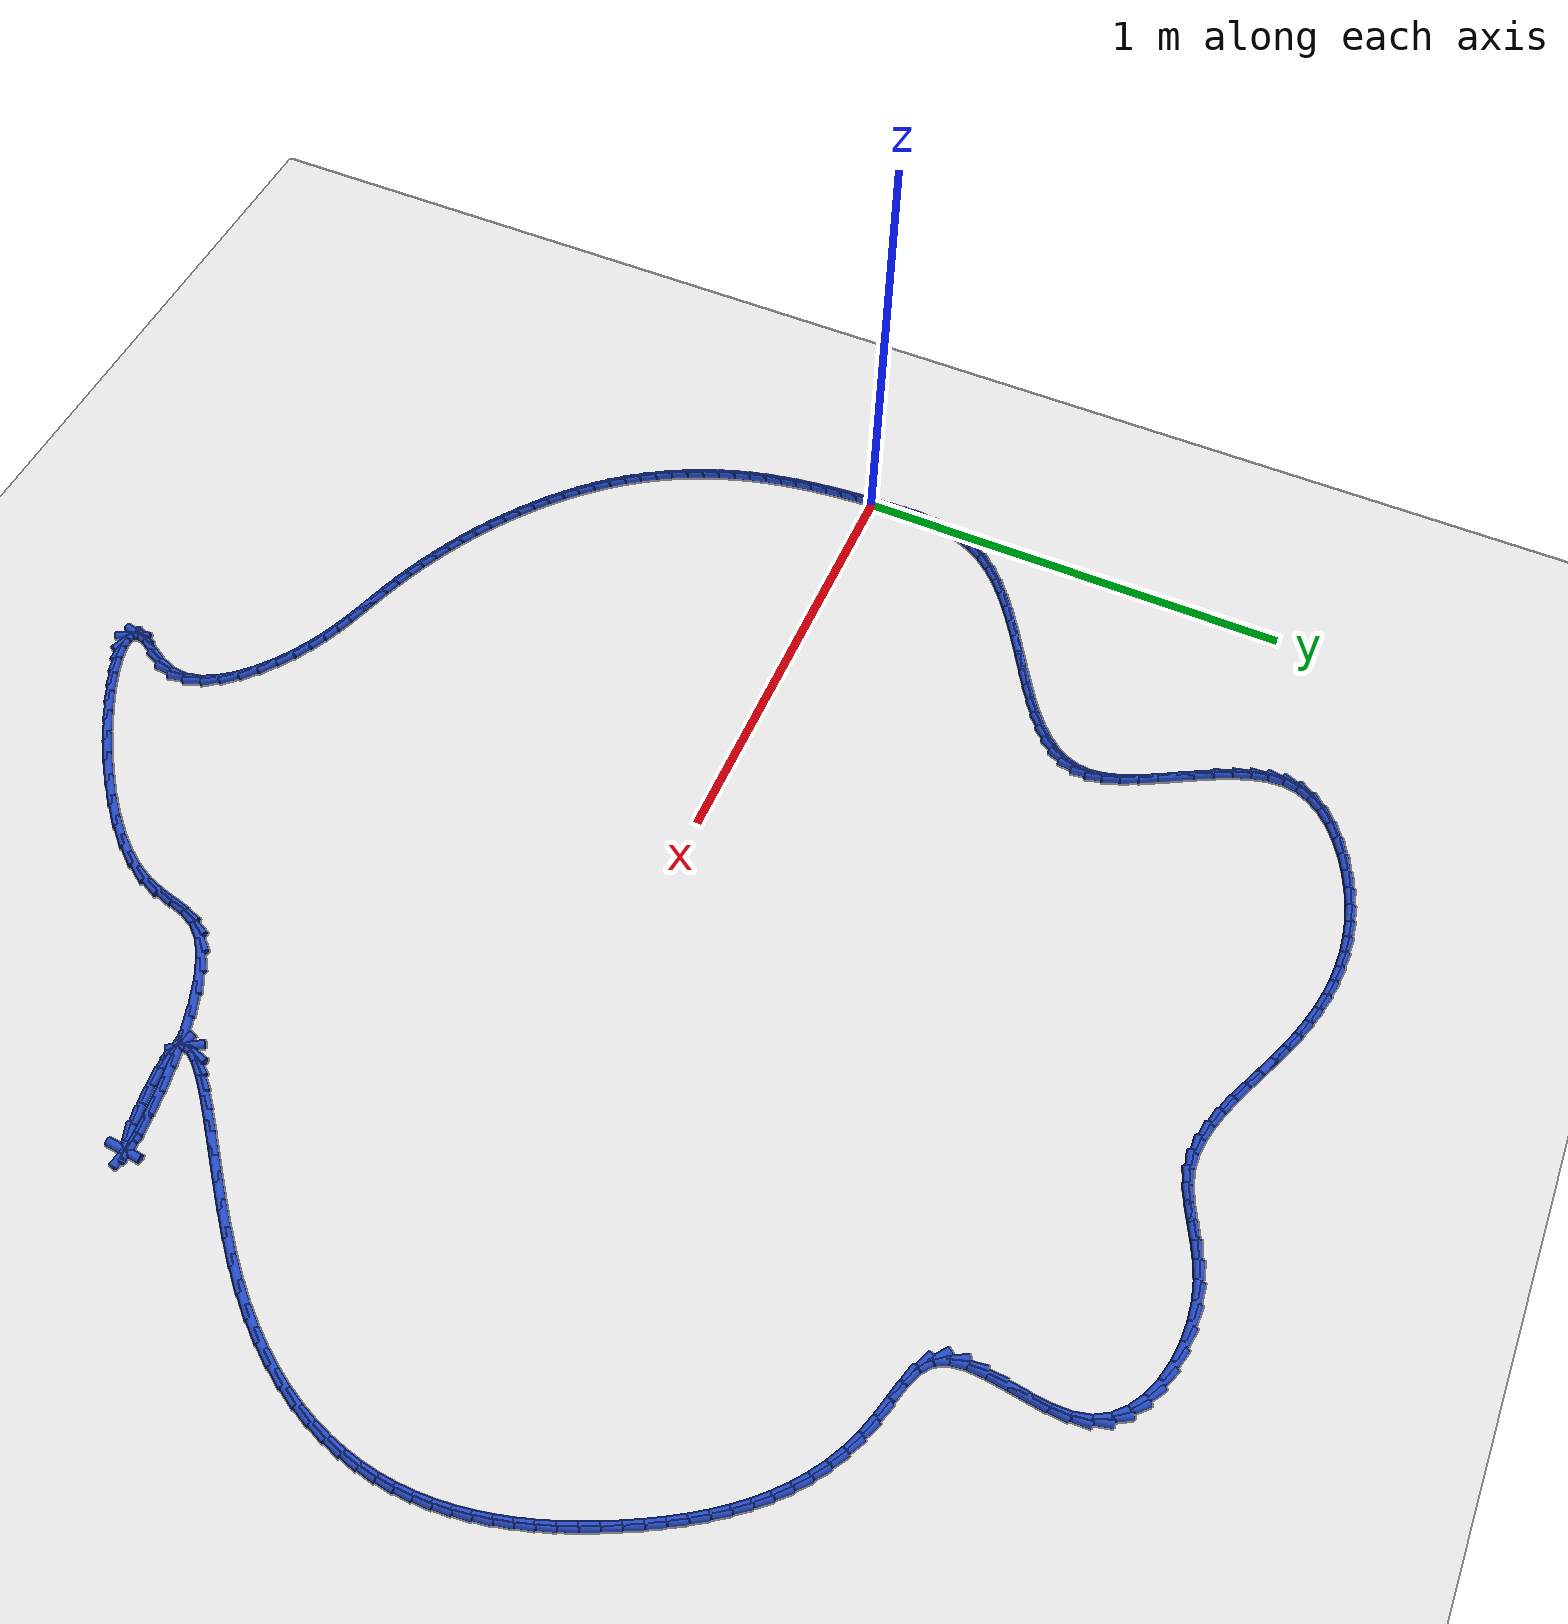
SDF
<sdf version="1.6">
 <world name="default">
  <light name="sun" type="directional">
   <pose>0 0 10 0 -0 0</pose>
   <diffuse>0.8 0.8 0.8 1</diffuse>
   <specular>0.2 0.2 0.2 1</specular>
   <attenuation>
    <range>1000</range>
    <constant>0.9</constant>
    <linear>0.01</linear>
    <quadratic>0.001</quadratic>
   </attenuation>
   <direction>-0.5 0.1 -0.9</direction>
  </light>
  <model name="ground_plane">
   <static>1</static>
   <link name="link">
    <collision name="collision">
     <geometry><plane><normal>0 0 1</normal><size>100 100</size></plane></geometry>
     <surface><friction><ode><mu>100</mu><mu2>50</mu2></ode></friction></surface>
    </collision>
    <visual name="visual">
     <cast_shadows>0</cast_shadows>
     <geometry><plane><normal>0 0 1</normal><size>100 100</size></plane></geometry>
     <material>
      <script><uri>file://media/materials/scripts/gazebo.material</uri><name>Gazebo/WhiteGlow</name></script>
     </material>
    </visual>
   </link>
  </model>
  <gravity>0 0 -9.8</gravity>
  <magnetic_field>6e-06 2.3e-05 -4.2e-05</magnetic_field>
  <atmosphere type="adiabatic"/>
  <physics name="default_physics" default="0" type="ode">
   <max_step_size>0.001</max_step_size>
   <real_time_factor>1</real_time_factor>
   <real_time_update_rate>1000</real_time_update_rate>
  </physics>
  <scene><ambient>0.4 0.4 0.4 1</ambient><background>0.7 0.7 0.7 1</background><shadows>1</shadows></scene>
  <spherical_coordinates>
   <surface_model>EARTH_WGS84</surface_model>
   <latitude_deg>0</latitude_deg>
   <longitude_deg>0</longitude_deg>
   <elevation>0</elevation>
   <heading_deg>0</heading_deg>
  </spherical_coordinates>
  <model name="line">
   <link name="link_0">
    <pose>2.5804011705155006e-17 4.85722573273506e-17 0.01 0 1.57 -1.5212838050681239</pose>
    <collision name="collision">
     <geometry><cylinder><radius>0.01</radius><length>0.08</length></cylinder></geometry>
    </collision>
    <visual name="visual">
     <material>
      <script><name>Gazebo/Blue</name><uri>file://media/materials/scripts/gazebo.material</uri></script>
     </material>
     <geometry><cylinder><radius>0.01</radius><length>0.08</length></cylinder></geometry>
    </visual>
   </link>
   <link name="link_1">
    <pose>-0.0019433137426240659 0.0392168568818954 0.01 0 1.57 -1.5498003176207837</pose>
    <collision name="collision">
     <geometry><cylinder><radius>0.01</radius><length>0.08</length></cylinder></geometry>
    </collision>
    <visual name="visual">
     <material>
      <script><name>Gazebo/Blue</name><uri>file://media/materials/scripts/gazebo.material</uri></script>
     </material>
     <geometry><cylinder><radius>0.01</radius><length>0.08</length></cylinder></geometry>
    </visual>
   </link>
   <link name="link_2">
    <pose>-0.0027694834000763996 0.07855996471965532 0.01 0 1.57 1.5458418137314556</pose>
    <collision name="collision">
     <geometry><cylinder><radius>0.01</radius><length>0.08</length></cylinder></geometry>
    </collision>
    <visual name="visual">
     <material>
      <script><name>Gazebo/Blue</name><uri>file://media/materials/scripts/gazebo.material</uri></script>
     </material>
     <geometry><cylinder><radius>0.01</radius><length>0.08</length></cylinder></geometry>
    </visual>
   </link>
   <link name="link_3">
    <pose>-0.0017938675187386993 0.11764761816727691 0.01 0 1.57 1.4809994952417194</pose>
    <collision name="collision">
     <geometry><cylinder><radius>0.01</radius><length>0.08</length></cylinder></geometry>
    </collision>
    <visual name="visual">
     <material>
      <script><name>Gazebo/Blue</name><uri>file://media/materials/scripts/gazebo.material</uri></script>
     </material>
     <geometry><cylinder><radius>0.01</radius><length>0.08</length></cylinder></geometry>
    </visual>
   </link>
   <link name="link_4">
    <pose>0.0016681753550073187 0.15609811187875713 0.01 0 1.57 1.395410960967276</pose>
    <collision name="collision">
     <geometry><cylinder><radius>0.01</radius><length>0.08</length></cylinder></geometry>
    </collision>
    <visual name="visual">
     <material>
      <script><name>Gazebo/Blue</name><uri>file://media/materials/scripts/gazebo.material</uri></script>
     </material>
     <geometry><cylinder><radius>0.01</radius><length>0.08</length></cylinder></geometry>
    </visual>
   </link>
   <link name="link_5">
    <pose>0.008301286674779926 0.1935297405080931 0.01 0 1.57 1.2875199271453694</pose>
    <collision name="collision">
     <geometry><cylinder><radius>0.01</radius><length>0.08</length></cylinder></geometry>
    </collision>
    <visual name="visual">
     <material>
      <script><name>Gazebo/Blue</name><uri>file://media/materials/scripts/gazebo.material</uri></script>
     </material>
     <geometry><cylinder><radius>0.01</radius><length>0.08</length></cylinder></geometry>
    </visual>
   </link>
   <link name="link_6">
    <pose>0.018790107894197414 0.22956079870928173 0.01 0 1.57 1.1572755042505294</pose>
    <collision name="collision">
     <geometry><cylinder><radius>0.01</radius><length>0.08</length></cylinder></geometry>
    </collision>
    <visual name="visual">
     <material>
      <script><name>Gazebo/Blue</name><uri>file://media/materials/scripts/gazebo.material</uri></script>
     </material>
     <geometry><cylinder><radius>0.01</radius><length>0.08</length></cylinder></geometry>
    </visual>
   </link>
   <link name="link_7">
    <pose>0.03381928046687805 0.2638095811363201 0.01 0 1.57 1.0113716114618447</pose>
    <collision name="collision">
     <geometry><cylinder><radius>0.01</radius><length>0.08</length></cylinder></geometry>
    </collision>
    <visual name="visual">
     <material>
      <script><name>Gazebo/Blue</name><uri>file://media/materials/scripts/gazebo.material</uri></script>
     </material>
     <geometry><cylinder><radius>0.01</radius><length>0.08</length></cylinder></geometry>
    </visual>
   </link>
   <link name="link_8">
    <pose>0.053944759830068384 0.2959512889091451 0.01 0 1.57 0.8801181496297427</pose>
    <collision name="collision">
     <geometry><cylinder><radius>0.01</radius><length>0.08</length></cylinder></geometry>
    </collision>
    <visual name="visual">
     <material>
      <script><name>Gazebo/Blue</name><uri>file://media/materials/scripts/gazebo.material</uri></script>
     </material>
     <geometry><cylinder><radius>0.01</radius><length>0.08</length></cylinder></geometry>
    </visual>
   </link>
   <link name="link_9">
    <pose>0.07882666081428817 0.32605727437229265 0.01 0 1.57 0.7747828723350667</pose>
    <collision name="collision">
     <geometry><cylinder><radius>0.01</radius><length>0.08</length></cylinder></geometry>
    </collision>
    <visual name="visual">
     <material>
      <script><name>Gazebo/Blue</name><uri>file://media/materials/scripts/gazebo.material</uri></script>
     </material>
     <geometry><cylinder><radius>0.01</radius><length>0.08</length></cylinder></geometry>
    </visual>
   </link>
   <link name="link_10">
    <pose>0.10774421695706923 0.3543673200458348 0.01 0 1.57 0.6928180842921344</pose>
    <collision name="collision">
     <geometry><cylinder><radius>0.01</radius><length>0.08</length></cylinder></geometry>
    </collision>
    <visual name="visual">
     <material>
      <script><name>Gazebo/Blue</name><uri>file://media/materials/scripts/gazebo.material</uri></script>
     </material>
     <geometry><cylinder><radius>0.01</radius><length>0.08</length></cylinder></geometry>
    </visual>
   </link>
   <link name="link_11">
    <pose>0.1399752656243701 0.3811218258532908 0.01 0 1.57 0.6309341611572226</pose>
    <collision name="collision">
     <geometry><cylinder><radius>0.01</radius><length>0.08</length></cylinder></geometry>
    </collision>
    <visual name="visual">
     <material>
      <script><name>Gazebo/Blue</name><uri>file://media/materials/scripts/gazebo.material</uri></script>
     </material>
     <geometry><cylinder><radius>0.01</radius><length>0.08</length></cylinder></geometry>
    </visual>
   </link>
   <link name="link_12">
    <pose>0.17479764418214916 0.40656119171818006 0.01 0 1.57 0.5861814027398884</pose>
    <collision name="collision">
     <geometry><cylinder><radius>0.01</radius><length>0.08</length></cylinder></geometry>
    </collision>
    <visual name="visual">
     <material>
      <script><name>Gazebo/Blue</name><uri>file://media/materials/scripts/gazebo.material</uri></script>
     </material>
     <geometry><cylinder><radius>0.01</radius><length>0.08</length></cylinder></geometry>
    </visual>
   </link>
   <link name="link_13">
    <pose>0.21148918999636473 0.4309258175640216 0.01 0 1.57 0.556338241644553</pose>
    <collision name="collision">
     <geometry><cylinder><radius>0.01</radius><length>0.08</length></cylinder></geometry>
    </collision>
    <visual name="visual">
     <material>
      <script><name>Gazebo/Blue</name><uri>file://media/materials/scripts/gazebo.material</uri></script>
     </material>
     <geometry><cylinder><radius>0.01</radius><length>0.08</length></cylinder></geometry>
    </visual>
   </link>
   <link name="link_14">
    <pose>0.24932774043297545 0.45445610331433495 0.01 0 1.57 0.5400025893214145</pose>
    <collision name="collision">
     <geometry><cylinder><radius>0.01</radius><length>0.08</length></cylinder></geometry>
    </collision>
    <visual name="visual">
     <material>
      <script><name>Gazebo/Blue</name><uri>file://media/materials/scripts/gazebo.material</uri></script>
     </material>
     <geometry><cylinder><radius>0.01</radius><length>0.08</length></cylinder></geometry>
    </visual>
   </link>
   <link name="link_15">
    <pose>0.2875911328579397 0.47739244889263915 0.01 0 1.57 0.5365985957737185</pose>
    <collision name="collision">
     <geometry><cylinder><radius>0.01</radius><length>0.08</length></cylinder></geometry>
    </collision>
    <visual name="visual">
     <material>
      <script><name>Gazebo/Blue</name><uri>file://media/materials/scripts/gazebo.material</uri></script>
     </material>
     <geometry><cylinder><radius>0.01</radius><length>0.08</length></cylinder></geometry>
    </visual>
   </link>
   <link name="link_16">
    <pose>0.3255572046372158 0.49997525422245376 0.01 0 1.57 0.5464024063301988</pose>
    <collision name="collision">
     <geometry><cylinder><radius>0.01</radius><length>0.08</length></cylinder></geometry>
    </collision>
    <visual name="visual">
     <material>
      <script><name>Gazebo/Blue</name><uri>file://media/materials/scripts/gazebo.material</uri></script>
     </material>
     <geometry><cylinder><radius>0.01</radius><length>0.08</length></cylinder></geometry>
    </visual>
   </link>
   <link name="link_17">
    <pose>0.36250379313676234 0.5224449192272977 0.01 0 1.57 0.5706372361215709</pose>
    <collision name="collision">
     <geometry><cylinder><radius>0.01</radius><length>0.08</length></cylinder></geometry>
    </collision>
    <visual name="visual">
     <material>
      <script><name>Gazebo/Blue</name><uri>file://media/materials/scripts/gazebo.material</uri></script>
     </material>
     <geometry><cylinder><radius>0.01</radius><length>0.08</length></cylinder></geometry>
    </visual>
   </link>
   <link name="link_18">
    <pose>0.3977087357225377 0.5450418438306904 0.01 0 1.57 0.611663975774591</pose>
    <collision name="collision">
     <geometry><cylinder><radius>0.01</radius><length>0.08</length></cylinder></geometry>
    </collision>
    <visual name="visual">
     <material>
      <script><name>Gazebo/Blue</name><uri>file://media/materials/scripts/gazebo.material</uri></script>
     </material>
     <geometry><cylinder><radius>0.01</radius><length>0.08</length></cylinder></geometry>
    </visual>
   </link>
   <link name="link_19">
    <pose>0.4304498697605002 0.5680064279561511 0.01 0 1.57 0.673264350154995</pose>
    <collision name="collision">
     <geometry><cylinder><radius>0.01</radius><length>0.08</length></cylinder></geometry>
    </collision>
    <visual name="visual">
     <material>
      <script><name>Gazebo/Blue</name><uri>file://media/materials/scripts/gazebo.material</uri></script>
     </material>
     <geometry><cylinder><radius>0.01</radius><length>0.08</length></cylinder></geometry>
    </visual>
   </link>
   <link name="link_20">
    <pose>0.46000503261660847 0.5915790715271991 0.01 0 1.57 0.76091789722028</pose>
    <collision name="collision">
     <geometry><cylinder><radius>0.01</radius><length>0.08</length></cylinder></geometry>
    </collision>
    <visual name="visual">
     <material>
      <script><name>Gazebo/Blue</name><uri>file://media/materials/scripts/gazebo.material</uri></script>
     </material>
     <geometry><cylinder><radius>0.01</radius><length>0.08</length></cylinder></geometry>
    </visual>
   </link>
   <link name="link_21">
    <pose>0.4856520616568209 0.6160001744673538 0.01 0 1.57 0.8816727600473289</pose>
    <collision name="collision">
     <geometry><cylinder><radius>0.01</radius><length>0.08</length></cylinder></geometry>
    </collision>
    <visual name="visual">
     <material>
      <script><name>Gazebo/Blue</name><uri>file://media/materials/scripts/gazebo.material</uri></script>
     </material>
     <geometry><cylinder><radius>0.01</radius><length>0.08</length></cylinder></geometry>
    </visual>
   </link>
   <link name="link_22">
    <pose>0.5066687942470958 0.641510136700134 0.01 0 1.57 1.042497816932174</pose>
    <collision name="collision">
     <geometry><cylinder><radius>0.01</radius><length>0.08</length></cylinder></geometry>
    </collision>
    <visual name="visual">
     <material>
      <script><name>Gazebo/Blue</name><uri>file://media/materials/scripts/gazebo.material</uri></script>
     </material>
     <geometry><cylinder><radius>0.01</radius><length>0.08</length></cylinder></geometry>
    </visual>
   </link>
   <link name="link_23">
    <pose>0.5223330677533917 0.6683493581490595 0.01 0 1.57 1.2452481862263058</pose>
    <collision name="collision">
     <geometry><cylinder><radius>0.01</radius><length>0.08</length></cylinder></geometry>
    </collision>
    <visual name="visual">
     <material>
      <script><name>Gazebo/Blue</name><uri>file://media/materials/scripts/gazebo.material</uri></script>
     </material>
     <geometry><cylinder><radius>0.01</radius><length>0.08</length></cylinder></geometry>
    </visual>
   </link>
   <link name="link_24">
    <pose>0.5319227195416673 0.6967582387376494 0.01 0 1.57 1.4786370363565953</pose>
    <collision name="collision">
     <geometry><cylinder><radius>0.01</radius><length>0.08</length></cylinder></geometry>
    </collision>
    <visual name="visual">
     <material>
      <script><name>Gazebo/Blue</name><uri>file://media/materials/scripts/gazebo.material</uri></script>
     </material>
     <geometry><cylinder><radius>0.01</radius><length>0.08</length></cylinder></geometry>
    </visual>
   </link>
   <link name="link_25">
    <pose>0.5347155869778804 0.7269771783894226 0.01 0 1.57 -1.435639426139682</pose>
    <collision name="collision">
     <geometry><cylinder><radius>0.01</radius><length>0.08</length></cylinder></geometry>
    </collision>
    <visual name="visual">
     <material>
      <script><name>Gazebo/Blue</name><uri>file://media/materials/scripts/gazebo.material</uri></script>
     </material>
     <geometry><cylinder><radius>0.01</radius><length>0.08</length></cylinder></geometry>
    </visual>
   </link>
   <link name="link_26">
    <pose>0.5303402059073712 0.7591524227633402 0.01 0 1.57 -1.2702528226170002</pose>
    <collision name="collision">
     <geometry><cylinder><radius>0.01</radius><length>0.08</length></cylinder></geometry>
    </collision>
    <visual name="visual">
     <material>
      <script><name>Gazebo/Blue</name><uri>file://media/materials/scripts/gazebo.material</uri></script>
     </material>
     <geometry><cylinder><radius>0.01</radius><length>0.08</length></cylinder></geometry>
    </visual>
   </link>
   <link name="link_27">
    <pose>0.5198336268215733 0.7930520645795267 0.01 0 1.57 -1.1630410028933769</pose>
    <collision name="collision">
     <geometry><cylinder><radius>0.01</radius><length>0.08</length></cylinder></geometry>
    </collision>
    <visual name="visual">
     <material>
      <script><name>Gazebo/Blue</name><uri>file://media/materials/scripts/gazebo.material</uri></script>
     </material>
     <geometry><cylinder><radius>0.01</radius><length>0.08</length></cylinder></geometry>
    </visual>
   </link>
   <link name="link_28">
    <pose>0.5045864648831673 0.8283492727886803 0.01 0 1.57 -1.0981016810550528</pose>
    <collision name="collision">
     <geometry><cylinder><radius>0.01</radius><length>0.08</length></cylinder></geometry>
    </collision>
    <visual name="visual">
     <material>
      <script><name>Gazebo/Blue</name><uri>file://media/materials/scripts/gazebo.material</uri></script>
     </material>
     <geometry><cylinder><radius>0.01</radius><length>0.08</length></cylinder></geometry>
    </visual>
   </link>
   <link name="link_29">
    <pose>0.48598933525571253 0.8647172163412631 0.01 0 1.57 -1.0649590709952692</pose>
    <collision name="collision">
     <geometry><cylinder><radius>0.01</radius><length>0.08</length></cylinder></geometry>
    </collision>
    <visual name="visual">
     <material>
      <script><name>Gazebo/Blue</name><uri>file://media/materials/scripts/gazebo.material</uri></script>
     </material>
     <geometry><cylinder><radius>0.01</radius><length>0.08</length></cylinder></geometry>
    </visual>
   </link>
   <link name="link_30">
    <pose>0.46543285310276833 0.9018290641877366 0.01 0 1.57 -1.0580992196619974</pose>
    <collision name="collision">
     <geometry><cylinder><radius>0.01</radius><length>0.08</length></cylinder></geometry>
    </collision>
    <visual name="visual">
     <material>
      <script><name>Gazebo/Blue</name><uri>file://media/materials/scripts/gazebo.material</uri></script>
     </material>
     <geometry><cylinder><radius>0.01</radius><length>0.08</length></cylinder></geometry>
    </visual>
   </link>
   <link name="link_31">
    <pose>0.4443076335878947 0.9393579852785632 0.01 0 1.57 -1.0758896131094773</pose>
    <collision name="collision">
     <geometry><cylinder><radius>0.01</radius><length>0.08</length></cylinder></geometry>
    </collision>
    <visual name="visual">
     <material>
      <script><name>Gazebo/Blue</name><uri>file://media/materials/scripts/gazebo.material</uri></script>
     </material>
     <geometry><cylinder><radius>0.01</radius><length>0.08</length></cylinder></geometry>
    </visual>
   </link>
   <link name="link_32">
    <pose>0.42400429187465083 0.9769771485642048 0.01 0 1.57 -1.1200806771920526</pose>
    <collision name="collision">
     <geometry><cylinder><radius>0.01</radius><length>0.08</length></cylinder></geometry>
    </collision>
    <visual name="visual">
     <material>
      <script><name>Gazebo/Blue</name><uri>file://media/materials/scripts/gazebo.material</uri></script>
     </material>
     <geometry><cylinder><radius>0.01</radius><length>0.08</length></cylinder></geometry>
    </visual>
   </link>
   <link name="link_33">
    <pose>0.4059134431265963 1.0143597229951231 0.01 0 1.57 -1.1959199596454844</pose>
    <collision name="collision">
     <geometry><cylinder><radius>0.01</radius><length>0.08</length></cylinder></geometry>
    </collision>
    <visual name="visual">
     <material>
      <script><name>Gazebo/Blue</name><uri>file://media/materials/scripts/gazebo.material</uri></script>
     </material>
     <geometry><cylinder><radius>0.01</radius><length>0.08</length></cylinder></geometry>
    </visual>
   </link>
   <link name="link_34">
    <pose>0.3914257025072906 1.0511788775217803 0.01 0 1.57 -1.3124565982221763</pose>
    <collision name="collision">
     <geometry><cylinder><radius>0.01</radius><length>0.08</length></cylinder></geometry>
    </collision>
    <visual name="visual">
     <material>
      <script><name>Gazebo/Blue</name><uri>file://media/materials/scripts/gazebo.material</uri></script>
     </material>
     <geometry><cylinder><radius>0.01</radius><length>0.08</length></cylinder></geometry>
    </visual>
   </link>
   <link name="link_35">
    <pose>0.38193168518029325 1.0871077810946386 0.01 0 1.57 -1.4814492521608806</pose>
    <collision name="collision">
     <geometry><cylinder><radius>0.01</radius><length>0.08</length></cylinder></geometry>
    </collision>
    <visual name="visual">
     <material>
      <script><name>Gazebo/Blue</name><uri>file://media/materials/scripts/gazebo.material</uri></script>
     </material>
     <geometry><cylinder><radius>0.01</radius><length>0.08</length></cylinder></geometry>
    </visual>
   </link>
   <link name="link_36">
    <pose>0.3788220063091639 1.1218196026641596 0.01 0 1.57 1.43107414136999</pose>
    <collision name="collision">
     <geometry><cylinder><radius>0.01</radius><length>0.08</length></cylinder></geometry>
    </collision>
    <visual name="visual">
     <material>
      <script><name>Gazebo/Blue</name><uri>file://media/materials/scripts/gazebo.material</uri></script>
     </material>
     <geometry><cylinder><radius>0.01</radius><length>0.08</length></cylinder></geometry>
    </visual>
   </link>
   <link name="link_37">
    <pose>0.3834866973733591 1.154987537452271 0.01 0 1.57 1.1714464519156043</pose>
    <collision name="collision">
     <geometry><cylinder><radius>0.01</radius><length>0.08</length></cylinder></geometry>
    </collision>
    <visual name="visual">
     <material>
      <script><name>Gazebo/Blue</name><uri>file://media/materials/scripts/gazebo.material</uri></script>
     </material>
     <geometry><cylinder><radius>0.01</radius><length>0.08</length></cylinder></geometry>
    </visual>
   </link>
   <link name="link_38">
    <pose>0.39670655453103376 1.1863122022002985 0.01 0 1.57 0.9529801354702475</pose>
    <collision name="collision">
     <geometry><cylinder><radius>0.01</radius><length>0.08</length></cylinder></geometry>
    </collision>
    <visual name="visual">
     <material>
      <script><name>Gazebo/Blue</name><uri>file://media/materials/scripts/gazebo.material</uri></script>
     </material>
     <geometry><cylinder><radius>0.01</radius><length>0.08</length></cylinder></geometry>
    </visual>
   </link>
   <link name="link_39">
    <pose>0.41750016089791586 1.2155735303888286 0.01 0 1.57 0.7839739822737973</pose>
    <collision name="collision">
     <geometry><cylinder><radius>0.01</radius><length>0.08</length></cylinder></geometry>
    </collision>
    <visual name="visual">
     <material>
      <script><name>Gazebo/Blue</name><uri>file://media/materials/scripts/gazebo.material</uri></script>
     </material>
     <geometry><cylinder><radius>0.01</radius><length>0.08</length></cylinder></geometry>
    </visual>
   </link>
   <link name="link_40">
    <pose>0.44456933664141324 1.2425657129143055 0.01 0 1.57 0.6530637935543421</pose>
    <collision name="collision">
     <geometry><cylinder><radius>0.01</radius><length>0.08</length></cylinder></geometry>
    </collision>
    <visual name="visual">
     <material>
      <script><name>Gazebo/Blue</name><uri>file://media/materials/scripts/gazebo.material</uri></script>
     </material>
     <geometry><cylinder><radius>0.01</radius><length>0.08</length></cylinder></geometry>
    </visual>
   </link>
   <link name="link_41">
    <pose>0.4766159019289341 1.2670829406731736 0.01 0 1.57 0.5486318522291008</pose>
    <collision name="collision">
     <geometry><cylinder><radius>0.01</radius><length>0.08</length></cylinder></geometry>
    </collision>
    <visual name="visual">
     <material>
      <script><name>Gazebo/Blue</name><uri>file://media/materials/scripts/gazebo.material</uri></script>
     </material>
     <geometry><cylinder><radius>0.01</radius><length>0.08</length></cylinder></geometry>
    </visual>
   </link>
   <link name="link_42">
    <pose>0.5123416769278868 1.2889194045618773 0.01 0 1.57 0.4614721665277679</pose>
    <collision name="collision">
     <geometry><cylinder><radius>0.01</radius><length>0.08</length></cylinder></geometry>
    </collision>
    <visual name="visual">
     <material>
      <script><name>Gazebo/Blue</name><uri>file://media/materials/scripts/gazebo.material</uri></script>
     </material>
     <geometry><cylinder><radius>0.01</radius><length>0.08</length></cylinder></geometry>
    </visual>
   </link>
   <link name="link_43">
    <pose>0.5504484818056792 1.3078692954768614 0.01 0 1.57 0.38449573136063264</pose>
    <collision name="collision">
     <geometry><cylinder><radius>0.01</radius><length>0.08</length></cylinder></geometry>
    </collision>
    <visual name="visual">
     <material>
      <script><name>Gazebo/Blue</name><uri>file://media/materials/scripts/gazebo.material</uri></script>
     </material>
     <geometry><cylinder><radius>0.01</radius><length>0.08</length></cylinder></geometry>
    </visual>
   </link>
   <link name="link_44">
    <pose>0.5896381367297198 1.323726804314571 0.01 0 1.57 0.31152956802972026</pose>
    <collision name="collision">
     <geometry><cylinder><radius>0.01</radius><length>0.08</length></cylinder></geometry>
    </collision>
    <visual name="visual">
     <material>
      <script><name>Gazebo/Blue</name><uri>file://media/materials/scripts/gazebo.material</uri></script>
     </material>
     <geometry><cylinder><radius>0.01</radius><length>0.08</length></cylinder></geometry>
    </visual>
   </link>
   <link name="link_45">
    <pose>0.6287358213996848 1.3363168393668832 0.01 0 1.57 0.2373969253806306</pose>
    <collision name="collision">
     <geometry><cylinder><radius>0.01</radius><length>0.08</length></cylinder></geometry>
    </collision>
    <visual name="visual">
     <material>
      <script><name>Gazebo/Blue</name><uri>file://media/materials/scripts/gazebo.material</uri></script>
     </material>
     <geometry><cylinder><radius>0.01</radius><length>0.08</length></cylinder></geometry>
    </visual>
   </link>
   <link name="link_46">
    <pose>0.6674286118320828 1.3456789272004055 0.01 0 1.57 0.16196937053756663</pose>
    <collision name="collision">
     <geometry><cylinder><radius>0.01</radius><length>0.08</length></cylinder></geometry>
    </collision>
    <visual name="visual">
     <material>
      <script><name>Gazebo/Blue</name><uri>file://media/materials/scripts/gazebo.material</uri></script>
     </material>
     <geometry><cylinder><radius>0.01</radius><length>0.08</length></cylinder></geometry>
    </visual>
   </link>
   <link name="link_47">
    <pose>0.7057712244809662 1.351944139449157 0.01 0 1.57 0.0865083251069434</pose>
    <collision name="collision">
     <geometry><cylinder><radius>0.01</radius><length>0.08</length></cylinder></geometry>
    </collision>
    <visual name="visual">
     <material>
      <script><name>Gazebo/Blue</name><uri>file://media/materials/scripts/gazebo.material</uri></script>
     </material>
     <geometry><cylinder><radius>0.01</radius><length>0.08</length></cylinder></geometry>
    </visual>
   </link>
   <link name="link_48">
    <pose>0.7438197455437329 1.3552438888229303 0.01 0 1.57 0.012316035726078168</pose>
    <collision name="collision">
     <geometry><cylinder><radius>0.01</radius><length>0.08</length></cylinder></geometry>
    </collision>
    <visual name="visual">
     <material>
      <script><name>Gazebo/Blue</name><uri>file://media/materials/scripts/gazebo.material</uri></script>
     </material>
     <geometry><cylinder><radius>0.01</radius><length>0.08</length></cylinder></geometry>
    </visual>
   </link>
   <link name="link_49">
    <pose>0.781630261217781 1.3557095880315186 0.01 0 1.57 -0.059377943456974634</pose>
    <collision name="collision">
     <geometry><cylinder><radius>0.01</radius><length>0.08</length></cylinder></geometry>
    </collision>
    <visual name="visual">
     <material>
      <script><name>Gazebo/Blue</name><uri>file://media/materials/scripts/gazebo.material</uri></script>
     </material>
     <geometry><cylinder><radius>0.01</radius><length>0.08</length></cylinder></geometry>
    </visual>
   </link>
   <link name="link_50">
    <pose>0.81925885770051 1.353472649784716 0.01 0 1.57 -0.12751261156599117</pose>
    <collision name="collision">
     <geometry><cylinder><radius>0.01</radius><length>0.08</length></cylinder></geometry>
    </collision>
    <visual name="visual">
     <material>
      <script><name>Gazebo/Blue</name><uri>file://media/materials/scripts/gazebo.material</uri></script>
     </material>
     <geometry><cylinder><radius>0.01</radius><length>0.08</length></cylinder></geometry>
    </visual>
   </link>
   <link name="link_51">
    <pose>0.8567616211893175 1.3486644867923152 0.01 0 1.57 -0.19125848973156906</pose>
    <collision name="collision">
     <geometry><cylinder><radius>0.01</radius><length>0.08</length></cylinder></geometry>
    </collision>
    <visual name="visual">
     <material>
      <script><name>Gazebo/Blue</name><uri>file://media/materials/scripts/gazebo.material</uri></script>
     </material>
     <geometry><cylinder><radius>0.01</radius><length>0.08</length></cylinder></geometry>
    </visual>
   </link>
   <link name="link_52">
    <pose>0.8941946378816017 1.3414165117641086 0.01 0 1.57 -0.25004124684386453</pose>
    <collision name="collision">
     <geometry><cylinder><radius>0.01</radius><length>0.08</length></cylinder></geometry>
    </collision>
    <visual name="visual">
     <material>
      <script><name>Gazebo/Blue</name><uri>file://media/materials/scripts/gazebo.material</uri></script>
     </material>
     <geometry><cylinder><radius>0.01</radius><length>0.08</length></cylinder></geometry>
    </visual>
   </link>
   <link name="link_53">
    <pose>0.9316139939747614 1.331860137409891 0.01 0 1.57 -0.30353050864730835</pose>
    <collision name="collision">
     <geometry><cylinder><radius>0.01</radius><length>0.08</length></cylinder></geometry>
    </collision>
    <visual name="visual">
     <material>
      <script><name>Gazebo/Blue</name><uri>file://media/materials/scripts/gazebo.material</uri></script>
     </material>
     <geometry><cylinder><radius>0.01</radius><length>0.08</length></cylinder></geometry>
    </visual>
   </link>
   <link name="link_54">
    <pose>0.9690757756661942 1.3201267764394538 0.01 0 1.57 -0.3515337976598853</pose>
    <collision name="collision">
     <geometry><cylinder><radius>0.01</radius><length>0.08</length></cylinder></geometry>
    </collision>
    <visual name="visual">
     <material>
      <script><name>Gazebo/Blue</name><uri>file://media/materials/scripts/gazebo.material</uri></script>
     </material>
     <geometry><cylinder><radius>0.01</radius><length>0.08</length></cylinder></geometry>
    </visual>
   </link>
   <link name="link_55">
    <pose>1.0066352988292842 1.3063511587819612 0.01 0 1.57 -0.3889637020447253</pose>
    <collision name="collision">
     <geometry><cylinder><radius>0.01</radius><length>0.08</length></cylinder></geometry>
    </collision>
    <visual name="visual">
     <material>
      <script><name>Gazebo/Blue</name><uri>file://media/materials/scripts/gazebo.material</uri></script>
     </material>
     <geometry><cylinder><radius>0.01</radius><length>0.08</length></cylinder></geometry>
    </visual>
   </link>
   <link name="link_56">
    <pose>1.0442896545424143 1.2909187457651587 0.01 0 1.57 -0.40818677197106557</pose>
    <collision name="collision">
     <geometry><cylinder><radius>0.01</radius><length>0.08</length></cylinder></geometry>
    </collision>
    <visual name="visual">
     <material>
      <script><name>Gazebo/Blue</name><uri>file://media/materials/scripts/gazebo.material</uri></script>
     </material>
     <geometry><cylinder><radius>0.01</radius><length>0.08</length></cylinder></geometry>
    </visual>
   </link>
   <link name="link_57">
    <pose>1.0819380080485415 1.2746366933174436 0.01 0 1.57 -0.4093604075994397</pose>
    <collision name="collision">
     <geometry><cylinder><radius>0.01</radius><length>0.08</length></cylinder></geometry>
    </collision>
    <visual name="visual">
     <material>
      <script><name>Gazebo/Blue</name><uri>file://media/materials/scripts/gazebo.material</uri></script>
     </material>
     <geometry><cylinder><radius>0.01</radius><length>0.08</length></cylinder></geometry>
    </visual>
   </link>
   <link name="link_58">
    <pose>1.1194701349047156 1.2583525918432656 0.01 0 1.57 -0.3923797090086689</pose>
    <collision name="collision">
     <geometry><cylinder><radius>0.01</radius><length>0.08</length></cylinder></geometry>
    </collision>
    <visual name="visual">
     <material>
      <script><name>Gazebo/Blue</name><uri>file://media/materials/scripts/gazebo.material</uri></script>
     </material>
     <geometry><cylinder><radius>0.01</radius><length>0.08</length></cylinder></geometry>
    </visual>
   </link>
   <link name="link_59">
    <pose>1.1567758106679884 1.2429140317470744 0.01 0 1.57 -0.35597065690690527</pose>
    <collision name="collision">
     <geometry><cylinder><radius>0.01</radius><length>0.08</length></cylinder></geometry>
    </collision>
    <visual name="visual">
     <material>
      <script><name>Gazebo/Blue</name><uri>file://media/materials/scripts/gazebo.material</uri></script>
     </material>
     <geometry><cylinder><radius>0.01</radius><length>0.08</length></cylinder></geometry>
    </visual>
   </link>
   <link name="link_60">
    <pose>1.1937448108954098 1.2291686034333198 0.01 0 1.57 -0.29767672948706325</pose>
    <collision name="collision">
     <geometry><cylinder><radius>0.01</radius><length>0.08</length></cylinder></geometry>
    </collision>
    <visual name="visual">
     <material>
      <script><name>Gazebo/Blue</name><uri>file://media/materials/scripts/gazebo.material</uri></script>
     </material>
     <geometry><cylinder><radius>0.01</radius><length>0.08</length></cylinder></geometry>
    </visual>
   </link>
   <link name="link_61">
    <pose>1.2302669111440323 1.2179638973064522 0.01 0 1.57 -0.21400547275993415</pose>
    <collision name="collision">
     <geometry><cylinder><radius>0.01</radius><length>0.08</length></cylinder></geometry>
    </collision>
    <visual name="visual">
     <material>
      <script><name>Gazebo/Blue</name><uri>file://media/materials/scripts/gazebo.material</uri></script>
     </material>
     <geometry><cylinder><radius>0.01</radius><length>0.08</length></cylinder></geometry>
    </visual>
   </link>
   <link name="link_62">
    <pose>1.2662318869709048 1.2101475037709202 0.01 0 1.57 -0.10109136592613818</pose>
    <collision name="collision">
     <geometry><cylinder><radius>0.01</radius><length>0.08</length></cylinder></geometry>
    </collision>
    <visual name="visual">
     <material>
      <script><name>Gazebo/Blue</name><uri>file://media/materials/scripts/gazebo.material</uri></script>
     </material>
     <geometry><cylinder><radius>0.01</radius><length>0.08</length></cylinder></geometry>
    </visual>
   </link>
   <link name="link_63">
    <pose>1.3015295139330803 1.206567013231175 0.01 0 1.57 0.043512509898410885</pose>
    <collision name="collision">
     <geometry><cylinder><radius>0.01</radius><length>0.08</length></cylinder></geometry>
    </collision>
    <visual name="visual">
     <material>
      <script><name>Gazebo/Blue</name><uri>file://media/materials/scripts/gazebo.material</uri></script>
     </material>
     <geometry><cylinder><radius>0.01</radius><length>0.08</length></cylinder></geometry>
    </visual>
   </link>
   <link name="link_64">
    <pose>1.3360495675876076 1.2080700160916658 0.01 0 1.57 0.21517340458693326</pose>
    <collision name="collision">
     <geometry><cylinder><radius>0.01</radius><length>0.08</length></cylinder></geometry>
    </collision>
    <visual name="visual">
     <material>
      <script><name>Gazebo/Blue</name><uri>file://media/materials/scripts/gazebo.material</uri></script>
     </material>
     <geometry><cylinder><radius>0.01</radius><length>0.08</length></cylinder></geometry>
    </visual>
   </link>
   <link name="link_65">
    <pose>1.3697058977985597 1.2154258390813983 0.01 0 1.57 0.3616135943402697</pose>
    <collision name="collision">
     <geometry><cylinder><radius>0.01</radius><length>0.08</length></cylinder></geometry>
    </collision>
    <visual name="visual">
     <material>
      <script><name>Gazebo/Blue</name><uri>file://media/materials/scripts/gazebo.material</uri></script>
     </material>
     <geometry><cylinder><radius>0.01</radius><length>0.08</length></cylinder></geometry>
    </visual>
   </link>
   <link name="link_66">
    <pose>1.4028551219848808 1.2279644064916635 0.01 0 1.57 0.4417007609927249</pose>
    <collision name="collision">
     <geometry><cylinder><radius>0.01</radius><length>0.08</length></cylinder></geometry>
    </collision>
    <visual name="visual">
     <material>
      <script><name>Gazebo/Blue</name><uri>file://media/materials/scripts/gazebo.material</uri></script>
     </material>
     <geometry><cylinder><radius>0.01</radius><length>0.08</length></cylinder></geometry>
    </visual>
   </link>
   <link name="link_67">
    <pose>1.4362425638824488 1.2437519890013964 0.01 0 1.57 0.46056815452773037</pose>
    <collision name="collision">
     <geometry><cylinder><radius>0.01</radius><length>0.08</length></cylinder></geometry>
    </collision>
    <visual name="visual">
     <material>
      <script><name>Gazebo/Blue</name><uri>file://media/materials/scripts/gazebo.material</uri></script>
     </material>
     <geometry><cylinder><radius>0.01</radius><length>0.08</length></cylinder></geometry>
    </visual>
   </link>
   <link name="link_68">
    <pose>1.470626751778296 1.260811930334041 0.01 0 1.57 0.4249892553250078</pose>
    <collision name="collision">
     <geometry><cylinder><radius>0.01</radius><length>0.08</length></cylinder></geometry>
    </collision>
    <visual name="visual">
     <material>
      <script><name>Gazebo/Blue</name><uri>file://media/materials/scripts/gazebo.material</uri></script>
     </material>
     <geometry><cylinder><radius>0.01</radius><length>0.08</length></cylinder></geometry>
    </visual>
   </link>
   <link name="link_69">
    <pose>1.5067662139594549 1.2771675742130422 0.01 0 1.57 0.34003690342998005</pose>
    <collision name="collision">
     <geometry><cylinder><radius>0.01</radius><length>0.08</length></cylinder></geometry>
    </collision>
    <visual name="visual">
     <material>
      <script><name>Gazebo/Blue</name><uri>file://media/materials/scripts/gazebo.material</uri></script>
     </material>
     <geometry><cylinder><radius>0.01</radius><length>0.08</length></cylinder></geometry>
    </visual>
   </link>
   <link name="link_70">
    <pose>1.5454194787129585 1.2908422643618451 0.01 0 1.57 0.21819469763228347</pose>
    <collision name="collision">
     <geometry><cylinder><radius>0.01</radius><length>0.08</length></cylinder></geometry>
    </collision>
    <visual name="visual">
     <material>
      <script><name>Gazebo/Blue</name><uri>file://media/materials/scripts/gazebo.material</uri></script>
     </material>
     <geometry><cylinder><radius>0.01</radius><length>0.08</length></cylinder></geometry>
    </visual>
   </link>
   <link name="link_71">
    <pose>1.5870935605710612 1.300082433772248 0.01 0 1.57 0.09835073592465911</pose>
    <collision name="collision">
     <geometry><cylinder><radius>0.01</radius><length>0.08</length></cylinder></geometry>
    </collision>
    <visual name="visual">
     <material>
      <script><name>Gazebo/Blue</name><uri>file://media/materials/scripts/gazebo.material</uri></script>
     </material>
     <geometry><cylinder><radius>0.01</radius><length>0.08</length></cylinder></geometry>
    </visual>
   </link>
   <link name="link_72">
    <pose>1.630867034209466 1.3044015220964715 0.01 0 1.57 -0.014439261064600915</pose>
    <collision name="collision">
     <geometry><cylinder><radius>0.01</radius><length>0.08</length></cylinder></geometry>
    </collision>
    <visual name="visual">
     <material>
      <script><name>Gazebo/Blue</name><uri>file://media/materials/scripts/gazebo.material</uri></script>
     </material>
     <geometry><cylinder><radius>0.01</radius><length>0.08</length></cylinder></geometry>
    </visual>
   </link>
   <link name="link_73">
    <pose>1.6753148419752804 1.3037596839896792 0.01 0 1.57 -0.12840980845523334</pose>
    <collision name="collision">
     <geometry><cylinder><radius>0.01</radius><length>0.08</length></cylinder></geometry>
    </collision>
    <visual name="visual">
     <material>
      <script><name>Gazebo/Blue</name><uri>file://media/materials/scripts/gazebo.material</uri></script>
     </material>
     <geometry><cylinder><radius>0.01</radius><length>0.08</length></cylinder></geometry>
    </visual>
   </link>
   <link name="link_74">
    <pose>1.7190113587376663 1.2981175774522316 0.01 0 1.57 -0.25180853218614735</pose>
    <collision name="collision">
     <geometry><cylinder><radius>0.01</radius><length>0.08</length></cylinder></geometry>
    </collision>
    <visual name="visual">
     <material>
      <script><name>Gazebo/Blue</name><uri>file://media/materials/scripts/gazebo.material</uri></script>
     </material>
     <geometry><cylinder><radius>0.01</radius><length>0.08</length></cylinder></geometry>
    </visual>
   </link>
   <link name="link_75">
    <pose>1.760530959365785 1.2874358604844882 0.01 0 1.57 -0.39393451230488924</pose>
    <collision name="collision">
     <geometry><cylinder><radius>0.01</radius><length>0.08</length></cylinder></geometry>
    </collision>
    <visual name="visual">
     <material>
      <script><name>Gazebo/Blue</name><uri>file://media/materials/scripts/gazebo.material</uri></script>
     </material>
     <geometry><cylinder><radius>0.01</radius><length>0.08</length></cylinder></geometry>
    </visual>
   </link>
   <link name="link_76">
    <pose>1.7984480187287977 1.2716751910868096 0.01 0 1.57 -0.5656392093929837</pose>
    <collision name="collision">
     <geometry><cylinder><radius>0.01</radius><length>0.08</length></cylinder></geometry>
    </collision>
    <visual name="visual">
     <material>
      <script><name>Gazebo/Blue</name><uri>file://media/materials/scripts/gazebo.material</uri></script>
     </material>
     <geometry><cylinder><radius>0.01</radius><length>0.08</length></cylinder></geometry>
    </visual>
   </link>
   <link name="link_77">
    <pose>1.831336911695866 1.2507962272595556 0.01 0 1.57 -0.7778037170647645</pose>
    <collision name="collision">
     <geometry><cylinder><radius>0.01</radius><length>0.08</length></cylinder></geometry>
    </collision>
    <visual name="visual">
     <material>
      <script><name>Gazebo/Blue</name><uri>file://media/materials/scripts/gazebo.material</uri></script>
     </material>
     <geometry><cylinder><radius>0.01</radius><length>0.08</length></cylinder></geometry>
    </visual>
   </link>
   <link name="link_78">
    <pose>1.8577720131361513 1.2247596270030874 0.01 0 1.57 -1.0347307177232772</pose>
    <collision name="collision">
     <geometry><cylinder><radius>0.01</radius><length>0.08</length></cylinder></geometry>
    </collision>
    <visual name="visual">
     <material>
      <script><name>Gazebo/Blue</name><uri>file://media/materials/scripts/gazebo.material</uri></script>
     </material>
     <geometry><cylinder><radius>0.01</radius><length>0.08</length></cylinder></geometry>
    </visual>
   </link>
   <link name="link_79">
    <pose>1.8763276979188148 1.1935260483177639 0.01 0 1.57 -1.314156795936497</pose>
    <collision name="collision">
     <geometry><cylinder><radius>0.01</radius><length>0.08</length></cylinder></geometry>
    </collision>
    <visual name="visual">
     <material>
      <script><name>Gazebo/Blue</name><uri>file://media/materials/scripts/gazebo.material</uri></script>
     </material>
     <geometry><cylinder><radius>0.01</radius><length>0.08</length></cylinder></geometry>
    </visual>
   </link>
   <link name="link_80">
    <pose>1.885866117556924 1.157179029040102 0.01 0 1.57 -1.522616961958107</pose>
    <collision name="collision">
     <geometry><cylinder><radius>0.01</radius><length>0.08</length></cylinder></geometry>
    </collision>
    <visual name="visual">
     <material>
      <script><name>Gazebo/Blue</name><uri>file://media/materials/scripts/gazebo.material</uri></script>
     </material>
     <geometry><cylinder><radius>0.01</radius><length>0.08</length></cylinder></geometry>
    </visual>
   </link>
   <link name="link_81">
    <pose>1.8878084882749646 1.1168948206062421 0.01 0 1.57 1.5028237638711182</pose>
    <collision name="collision">
     <geometry><cylinder><radius>0.01</radius><length>0.08</length></cylinder></geometry>
    </collision>
    <visual name="visual">
     <material>
      <script><name>Gazebo/Blue</name><uri>file://media/materials/scripts/gazebo.material</uri></script>
     </material>
     <geometry><cylinder><radius>0.01</radius><length>0.08</length></cylinder></geometry>
    </visual>
   </link>
   <link name="link_82">
    <pose>1.8849170674591547 1.0744222953432883 0.01 0 1.57 1.4559115623039205</pose>
    <collision name="collision">
     <geometry><cylinder><radius>0.01</radius><length>0.08</length></cylinder></geometry>
    </collision>
    <visual name="visual">
     <material>
      <script><name>Gazebo/Blue</name><uri>file://media/materials/scripts/gazebo.material</uri></script>
     </material>
     <geometry><cylinder><radius>0.01</radius><length>0.08</length></cylinder></geometry>
    </visual>
   </link>
   <link name="link_83">
    <pose>1.8799659129878576 1.0315153643560626 0.01 0 1.57 1.4692689374037364</pose>
    <collision name="collision">
     <geometry><cylinder><radius>0.01</radius><length>0.08</length></cylinder></geometry>
    </collision>
    <visual name="visual">
     <material>
      <script><name>Gazebo/Blue</name><uri>file://media/materials/scripts/gazebo.material</uri></script>
     </material>
     <geometry><cylinder><radius>0.01</radius><length>0.08</length></cylinder></geometry>
    </visual>
   </link>
   <link name="link_84">
    <pose>1.8757290827394386 0.9899279387493893 0.01 0 1.57 1.5513656321150724</pose>
    <collision name="collision">
     <geometry><cylinder><radius>0.01</radius><length>0.08</length></cylinder></geometry>
    </collision>
    <visual name="visual">
     <material>
      <script><name>Gazebo/Blue</name><uri>file://media/materials/scripts/gazebo.material</uri></script>
     </material>
     <geometry><cylinder><radius>0.01</radius><length>0.08</length></cylinder></geometry>
    </visual>
   </link>
   <link name="link_85">
    <pose>1.8749806345922635 0.951413929628091 0.01 0 1.57 -1.408550490958973</pose>
    <collision name="collision">
     <geometry><cylinder><radius>0.01</radius><length>0.08</length></cylinder></geometry>
    </collision>
    <visual name="visual">
     <material>
      <script><name>Gazebo/Blue</name><uri>file://media/materials/scripts/gazebo.material</uri></script>
     </material>
     <geometry><cylinder><radius>0.01</radius><length>0.08</length></cylinder></geometry>
    </visual>
   </link>
   <link name="link_86">
    <pose>1.8804946264246958 0.917727248096991 0.01 0 1.57 -1.0781356769096497</pose>
    <collision name="collision">
     <geometry><cylinder><radius>0.01</radius><length>0.08</length></cylinder></geometry>
    </collision>
    <visual name="visual">
     <material>
      <script><name>Gazebo/Blue</name><uri>file://media/materials/scripts/gazebo.material</uri></script>
     </material>
     <geometry><cylinder><radius>0.01</radius><length>0.08</length></cylinder></geometry>
    </visual>
   </link>
   <link name="link_87">
    <pose>1.895045116115102 0.8906218052609131 0.01 0 1.57 -0.6507181890787552</pose>
    <collision name="collision">
     <geometry><cylinder><radius>0.01</radius><length>0.08</length></cylinder></geometry>
    </collision>
    <visual name="visual">
     <material>
      <script><name>Gazebo/Blue</name><uri>file://media/materials/scripts/gazebo.material</uri></script>
     </material>
     <geometry><cylinder><radius>0.01</radius><length>0.08</length></cylinder></geometry>
    </visual>
   </link>
   <link name="link_88">
    <pose>1.9205329517024785 0.871216940949451 0.01 0 1.57 -0.3788224263739764</pose>
    <collision name="collision">
     <geometry><cylinder><radius>0.01</radius><length>0.08</length></cylinder></geometry>
    </collision>
    <visual name="visual">
     <material>
      <script><name>Gazebo/Blue</name><uri>file://media/materials/scripts/gazebo.material</uri></script>
     </material>
     <geometry><cylinder><radius>0.01</radius><length>0.08</length></cylinder></geometry>
    </visual>
   </link>
   <link name="link_89">
    <pose>1.9547064021600142 0.8576142697279223 0.01 0 1.57 -0.2628575783158508</pose>
    <collision name="collision">
     <geometry><cylinder><radius>0.01</radius><length>0.08</length></cylinder></geometry>
    </collision>
    <visual name="visual">
     <material>
      <script><name>Gazebo/Blue</name><uri>file://media/materials/scripts/gazebo.material</uri></script>
     </material>
     <geometry><cylinder><radius>0.01</radius><length>0.08</length></cylinder></geometry>
    </visual>
   </link>
   <link name="link_90">
    <pose>1.9940806436527088 0.8470193039414307 0.01 0 1.57 -0.24748269689805905</pose>
    <collision name="collision">
     <geometry><cylinder><radius>0.01</radius><length>0.08</length></cylinder></geometry>
    </collision>
    <visual name="visual">
     <material>
      <script><name>Gazebo/Blue</name><uri>file://media/materials/scripts/gazebo.material</uri></script>
     </material>
     <geometry><cylinder><radius>0.01</radius><length>0.08</length></cylinder></geometry>
    </visual>
   </link>
   <link name="link_91">
    <pose>2.035170653392199 0.8366374113534671 0.01 0 1.57 -0.31092048991335297</pose>
    <collision name="collision">
     <geometry><cylinder><radius>0.01</radius><length>0.08</length></cylinder></geometry>
    </collision>
    <visual name="visual">
     <material>
      <script><name>Gazebo/Blue</name><uri>file://media/materials/scripts/gazebo.material</uri></script>
     </material>
     <geometry><cylinder><radius>0.01</radius><length>0.08</length></cylinder></geometry>
    </visual>
   </link>
   <link name="link_92">
    <pose>2.0747746166040058 0.8239109650690902 0.01 0 1.57 -0.4008113588093068</pose>
    <collision name="collision">
     <geometry><cylinder><radius>0.01</radius><length>0.08</length></cylinder></geometry>
    </collision>
    <visual name="visual">
     <material>
      <script><name>Gazebo/Blue</name><uri>file://media/materials/scripts/gazebo.material</uri></script>
     </material>
     <geometry><cylinder><radius>0.01</radius><length>0.08</length></cylinder></geometry>
    </visual>
   </link>
   <link name="link_93">
    <pose>2.111937989169559 0.8081629881866321 0.01 0 1.57 -0.48927371327625657</pose>
    <collision name="collision">
     <geometry><cylinder><radius>0.01</radius><length>0.08</length></cylinder></geometry>
    </collision>
    <visual name="visual">
     <material>
      <script><name>Gazebo/Blue</name><uri>file://media/materials/scripts/gazebo.material</uri></script>
     </material>
     <geometry><cylinder><radius>0.01</radius><length>0.08</length></cylinder></geometry>
    </visual>
   </link>
   <link name="link_94">
    <pose>2.1467771253390002 0.7896126953711188 0.01 0 1.57 -0.5745055446254678</pose>
    <collision name="collision">
     <geometry><cylinder><radius>0.01</radius><length>0.08</length></cylinder></geometry>
    </collision>
    <visual name="visual">
     <material>
      <script><name>Gazebo/Blue</name><uri>file://media/materials/scripts/gazebo.material</uri></script>
     </material>
     <geometry><cylinder><radius>0.01</radius><length>0.08</length></cylinder></geometry>
    </visual>
   </link>
   <link name="link_95">
    <pose>2.1794149554623425 0.7684848045598015 0.01 0 1.57 -0.6551505645496015</pose>
    <collision name="collision">
     <geometry><cylinder><radius>0.01</radius><length>0.08</length></cylinder></geometry>
    </collision>
    <visual name="visual">
     <material>
      <script><name>Gazebo/Blue</name><uri>file://media/materials/scripts/gazebo.material</uri></script>
     </material>
     <geometry><cylinder><radius>0.01</radius><length>0.08</length></cylinder></geometry>
    </visual>
   </link>
   <link name="link_96">
    <pose>2.2099744098896 0.7450040336899306 0.01 0 1.57 -0.7302077535805038</pose>
    <collision name="collision">
     <geometry><cylinder><radius>0.01</radius><length>0.08</length></cylinder></geometry>
    </collision>
    <visual name="visual">
     <material>
      <script><name>Gazebo/Blue</name><uri>file://media/materials/scripts/gazebo.material</uri></script>
     </material>
     <geometry><cylinder><radius>0.01</radius><length>0.08</length></cylinder></geometry>
    </visual>
   </link>
   <link name="link_97">
    <pose>2.2385784189707834 0.7193951006987568 0.01 0 1.57 -0.7990456258027642</pose>
    <collision name="collision">
     <geometry><cylinder><radius>0.01</radius><length>0.08</length></cylinder></geometry>
    </collision>
    <visual name="visual">
     <material>
      <script><name>Gazebo/Blue</name><uri>file://media/materials/scripts/gazebo.material</uri></script>
     </material>
     <geometry><cylinder><radius>0.01</radius><length>0.08</length></cylinder></geometry>
    </visual>
   </link>
   <link name="link_98">
    <pose>2.265349913055908 0.691882723523531 0.01 0 1.57 -0.861361658678026</pose>
    <collision name="collision">
     <geometry><cylinder><radius>0.01</radius><length>0.08</length></cylinder></geometry>
    </collision>
    <visual name="visual">
     <material>
      <script><name>Gazebo/Blue</name><uri>file://media/materials/scripts/gazebo.material</uri></script>
     </material>
     <geometry><cylinder><radius>0.01</radius><length>0.08</length></cylinder></geometry>
    </visual>
   </link>
   <link name="link_99">
    <pose>2.2904118224949865 0.6626916201015031 0.01 0 1.57 -0.9171109996088366</pose>
    <collision name="collision">
     <geometry><cylinder><radius>0.01</radius><length>0.08</length></cylinder></geometry>
    </collision>
    <visual name="visual">
     <material>
      <script><name>Gazebo/Blue</name><uri>file://media/materials/scripts/gazebo.material</uri></script>
     </material>
     <geometry><cylinder><radius>0.01</radius><length>0.08</length></cylinder></geometry>
    </visual>
   </link>
   <link name="link_100">
    <pose>2.3138870776380314 0.6320465083699249 0.01 0 1.57 -0.9664267605133154</pose>
    <collision name="collision">
     <geometry><cylinder><radius>0.01</radius><length>0.08</length></cylinder></geometry>
    </collision>
    <visual name="visual">
     <material>
      <script><name>Gazebo/Blue</name><uri>file://media/materials/scripts/gazebo.material</uri></script>
     </material>
     <geometry><cylinder><radius>0.01</radius><length>0.08</length></cylinder></geometry>
    </visual>
   </link>
   <link name="link_101">
    <pose>2.3358986088350573 0.6001721062660461 0.01 0 1.57 -1.009546726760588</pose>
    <collision name="collision">
     <geometry><cylinder><radius>0.01</radius><length>0.08</length></cylinder></geometry>
    </collision>
    <visual name="visual">
     <material>
      <script><name>Gazebo/Blue</name><uri>file://media/materials/scripts/gazebo.material</uri></script>
     </material>
     <geometry><cylinder><radius>0.01</radius><length>0.08</length></cylinder></geometry>
    </visual>
   </link>
   <link name="link_102">
    <pose>2.356569346436075 0.567293131727118 0.01 0 1.57 -1.0467533460196503</pose>
    <collision name="collision">
     <geometry><cylinder><radius>0.01</radius><length>0.08</length></cylinder></geometry>
    </collision>
    <visual name="visual">
     <material>
      <script><name>Gazebo/Blue</name><uri>file://media/materials/scripts/gazebo.material</uri></script>
     </material>
     <geometry><cylinder><radius>0.01</radius><length>0.08</length></cylinder></geometry>
    </visual>
   </link>
   <link name="link_103">
    <pose>2.376022220791101 0.5336343026903909 0.01 0 1.57 -1.078332419767399</pose>
    <collision name="collision">
     <geometry><cylinder><radius>0.01</radius><length>0.08</length></cylinder></geometry>
    </collision>
    <visual name="visual">
     <material>
      <script><name>Gazebo/Blue</name><uri>file://media/materials/scripts/gazebo.material</uri></script>
     </material>
     <geometry><cylinder><radius>0.01</radius><length>0.08</length></cylinder></geometry>
    </visual>
   </link>
   <link name="link_104">
    <pose>2.3943800308982817 0.49942022516066953 0.01 0 1.57 -1.1065879782315884</pose>
    <collision name="collision">
     <geometry><cylinder><radius>0.01</radius><length>0.08</length></cylinder></geometry>
    </collision>
    <visual name="visual">
     <material>
      <script><name>Gazebo/Blue</name><uri>file://media/materials/scripts/gazebo.material</uri></script>
     </material>
     <geometry><cylinder><radius>0.01</radius><length>0.08</length></cylinder></geometry>
    </visual>
   </link>
   <link name="link_105">
    <pose>2.41170321765218 0.464822366230679 0.01 0 1.57 -1.1370400719894822</pose>
    <collision name="collision">
     <geometry><cylinder><radius>0.01</radius><length>0.08</length></cylinder></geometry>
    </collision>
    <visual name="visual">
     <material>
      <script><name>Gazebo/Blue</name><uri>file://media/materials/scripts/gazebo.material</uri></script>
     </material>
     <geometry><cylinder><radius>0.01</radius><length>0.08</length></cylinder></geometry>
    </visual>
   </link>
   <link name="link_106">
    <pose>2.427890326713249 0.42987423279045006 0.01 0 1.57 -1.170687186168735</pose>
    <collision name="collision">
     <geometry><cylinder><radius>0.01</radius><length>0.08</length></cylinder></geometry>
    </collision>
    <visual name="visual">
     <material>
      <script><name>Gazebo/Blue</name><uri>file://media/materials/scripts/gazebo.material</uri></script>
     </material>
     <geometry><cylinder><radius>0.01</radius><length>0.08</length></cylinder></geometry>
    </visual>
   </link>
   <link name="link_107">
    <pose>2.4428139708779084 0.3945872328510779 0.01 0 1.57 -1.2076665442976666</pose>
    <collision name="collision">
     <geometry><cylinder><radius>0.01</radius><length>0.08</length></cylinder></geometry>
    </collision>
    <visual name="visual">
     <material>
      <script><name>Gazebo/Blue</name><uri>file://media/materials/scripts/gazebo.material</uri></script>
     </material>
     <geometry><cylinder><radius>0.01</radius><length>0.08</length></cylinder></geometry>
    </visual>
   </link>
   <link name="link_108">
    <pose>2.4563467629425797 0.35897277442365755 0.01 0 1.57 -1.2481013349724457</pose>
    <collision name="collision">
     <geometry><cylinder><radius>0.01</radius><length>0.08</length></cylinder></geometry>
    </collision>
    <visual name="visual">
     <material>
      <script><name>Gazebo/Blue</name><uri>file://media/materials/scripts/gazebo.material</uri></script>
     </material>
     <geometry><cylinder><radius>0.01</radius><length>0.08</length></cylinder></geometry>
    </visual>
   </link>
   <link name="link_109">
    <pose>2.4683613157036826 0.3230422655192855 0.01 0 1.57 -1.292087820820157</pose>
    <collision name="collision">
     <geometry><cylinder><radius>0.01</radius><length>0.08</length></cylinder></geometry>
    </collision>
    <visual name="visual">
     <material>
      <script><name>Gazebo/Blue</name><uri>file://media/materials/scripts/gazebo.material</uri></script>
     </material>
     <geometry><cylinder><radius>0.01</radius><length>0.08</length></cylinder></geometry>
    </visual>
   </link>
   <link name="link_110">
    <pose>2.4787302419576376 0.2868071141490565 0.01 0 1.57 -1.3396797657786215</pose>
    <collision name="collision">
     <geometry><cylinder><radius>0.01</radius><length>0.08</length></cylinder></geometry>
    </collision>
    <visual name="visual">
     <material>
      <script><name>Gazebo/Blue</name><uri>file://media/materials/scripts/gazebo.material</uri></script>
     </material>
     <geometry><cylinder><radius>0.01</radius><length>0.08</length></cylinder></geometry>
    </visual>
   </link>
   <link name="link_111">
    <pose>2.487326154500865 0.250278728324067 0.01 0 1.57 -1.3908706225121452</pose>
    <collision name="collision">
     <geometry><cylinder><radius>0.01</radius><length>0.08</length></cylinder></geometry>
    </collision>
    <visual name="visual">
     <material>
      <script><name>Gazebo/Blue</name><uri>file://media/materials/scripts/gazebo.material</uri></script>
     </material>
     <geometry><cylinder><radius>0.01</radius><length>0.08</length></cylinder></geometry>
    </visual>
   </link>
   <link name="link_112">
    <pose>2.494021666129785 0.21346851605541162 0.01 0 1.57 -1.4455746005712309</pose>
    <collision name="collision">
     <geometry><cylinder><radius>0.01</radius><length>0.08</length></cylinder></geometry>
    </collision>
    <visual name="visual">
     <material>
      <script><name>Gazebo/Blue</name><uri>file://media/materials/scripts/gazebo.material</uri></script>
     </material>
     <geometry><cylinder><radius>0.01</radius><length>0.08</length></cylinder></geometry>
    </visual>
   </link>
   <link name="link_113">
    <pose>2.4986893896408193 0.17638788535418692 0.01 0 1.57 -1.5036085803015755</pose>
    <collision name="collision">
     <geometry><cylinder><radius>0.01</radius><length>0.08</length></cylinder></geometry>
    </collision>
    <visual name="visual">
     <material>
      <script><name>Gazebo/Blue</name><uri>file://media/materials/scripts/gazebo.material</uri></script>
     </material>
     <geometry><cylinder><radius>0.01</radius><length>0.08</length></cylinder></geometry>
    </visual>
   </link>
   <link name="link_114">
    <pose>2.501201937830386 0.13904824423148737 0.01 0 1.57 -1.5646776872553143</pose>
    <collision name="collision">
     <geometry><cylinder><radius>0.01</radius><length>0.08</length></cylinder></geometry>
    </collision>
    <visual name="visual">
     <material>
      <script><name>Gazebo/Blue</name><uri>file://media/materials/scripts/gazebo.material</uri></script>
     </material>
     <geometry><cylinder><radius>0.01</radius><length>0.08</length></cylinder></geometry>
    </visual>
   </link>
   <link name="link_115">
    <pose>2.501431923494907 0.1014610006984096 0.01 0 1.57 1.5132247478090395</pose>
    <collision name="collision">
     <geometry><cylinder><radius>0.01</radius><length>0.08</length></cylinder></geometry>
    </collision>
    <visual name="visual">
     <material>
      <script><name>Gazebo/Blue</name><uri>file://media/materials/scripts/gazebo.material</uri></script>
     </material>
     <geometry><cylinder><radius>0.01</radius><length>0.08</length></cylinder></geometry>
    </visual>
   </link>
   <link name="link_116">
    <pose>2.499251959430802 0.06363756276604876 0.01 0 1.57 1.4474436394096408</pose>
    <collision name="collision">
     <geometry><cylinder><radius>0.01</radius><length>0.08</length></cylinder></geometry>
    </collision>
    <visual name="visual">
     <material>
      <script><name>Gazebo/Blue</name><uri>file://media/materials/scripts/gazebo.material</uri></script>
     </material>
     <geometry><cylinder><radius>0.01</radius><length>0.08</length></cylinder></geometry>
    </visual>
   </link>
   <link name="link_117">
    <pose>2.4945346584344925 0.025589338445499384 0.01 0 1.57 1.380202598604492</pose>
    <collision name="collision">
     <geometry><cylinder><radius>0.01</radius><length>0.08</length></cylinder></geometry>
    </collision>
    <visual name="visual">
     <material>
      <script><name>Gazebo/Blue</name><uri>file://media/materials/scripts/gazebo.material</uri></script>
     </material>
     <geometry><cylinder><radius>0.01</radius><length>0.08</length></cylinder></geometry>
    </visual>
   </link>
   <link name="link_118">
    <pose>2.487152633302397 -0.012672264252141019 0.01 0 1.57 1.3122051764016978</pose>
    <collision name="collision">
     <geometry><cylinder><radius>0.01</radius><length>0.08</length></cylinder></geometry>
    </collision>
    <visual name="visual">
     <material>
      <script><name>Gazebo/Blue</name><uri>file://media/materials/scripts/gazebo.material</uri></script>
     </material>
     <geometry><cylinder><radius>0.01</radius><length>0.08</length></cylinder></geometry>
    </visual>
   </link>
   <link name="link_119">
    <pose>2.476978496830938 -0.051135837315777866 0.01 0 1.57 1.2441892411514186</pose>
    <collision name="collision">
     <geometry><cylinder><radius>0.01</radius><length>0.08</length></cylinder></geometry>
    </collision>
    <visual name="visual">
     <material>
      <script><name>Gazebo/Blue</name><uri>file://media/materials/scripts/gazebo.material</uri></script>
     </material>
     <geometry><cylinder><radius>0.01</radius><length>0.08</length></cylinder></geometry>
    </visual>
   </link>
   <link name="link_120">
    <pose>2.4638848618165357 -0.0897899727343156 0.01 0 1.57 1.1768835640171562</pose>
    <collision name="collision">
     <geometry><cylinder><radius>0.01</radius><length>0.08</length></cylinder></geometry>
    </collision>
    <visual name="visual">
     <material>
      <script><name>Gazebo/Blue</name><uri>file://media/materials/scripts/gazebo.material</uri></script>
     </material>
     <geometry><cylinder><radius>0.01</radius><length>0.08</length></cylinder></geometry>
    </visual>
   </link>
   <link name="link_121">
    <pose>2.447744341055608 -0.12862326249665848 0.01 0 1.57 1.1109655985138451</pose>
    <collision name="collision">
     <geometry><cylinder><radius>0.01</radius><length>0.08</length></cylinder></geometry>
    </collision>
    <visual name="visual">
     <material>
      <script><name>Gazebo/Blue</name><uri>file://media/materials/scripts/gazebo.material</uri></script>
     </material>
     <geometry><cylinder><radius>0.01</radius><length>0.08</length></cylinder></geometry>
    </visual>
   </link>
   <link name="link_122">
    <pose>2.4284295473445776 -0.16762429859171218 0.01 0 1.57 1.0470264661426645</pose>
    <collision name="collision">
     <geometry><cylinder><radius>0.01</radius><length>0.08</length></cylinder></geometry>
    </collision>
    <visual name="visual">
     <material>
      <script><name>Gazebo/Blue</name><uri>file://media/materials/scripts/gazebo.material</uri></script>
     </material>
     <geometry><cylinder><radius>0.01</radius><length>0.08</length></cylinder></geometry>
    </visual>
   </link>
   <link name="link_123">
    <pose>2.405813093479864 -0.20678167300837902 0.01 0 1.57 0.985547313494991</pose>
    <collision name="collision">
     <geometry><cylinder><radius>0.01</radius><length>0.08</length></cylinder></geometry>
    </collision>
    <visual name="visual">
     <material>
      <script><name>Gazebo/Blue</name><uri>file://media/materials/scripts/gazebo.material</uri></script>
     </material>
     <geometry><cylinder><radius>0.01</radius><length>0.08</length></cylinder></geometry>
    </visual>
   </link>
   <link name="link_124">
    <pose>2.3797675922578883 -0.24608397773556434 0.01 0 1.57 0.9268885564496673</pose>
    <collision name="collision">
     <geometry><cylinder><radius>0.01</radius><length>0.08</length></cylinder></geometry>
    </collision>
    <visual name="visual">
     <material>
      <script><name>Gazebo/Blue</name><uri>file://media/materials/scripts/gazebo.material</uri></script>
     </material>
     <geometry><cylinder><radius>0.01</radius><length>0.08</length></cylinder></geometry>
    </visual>
   </link>
   <link name="link_125">
    <pose>2.35016565647507 -0.28551980476217265 0.01 0 1.57 0.8712909964603617</pose>
    <collision name="collision">
     <geometry><cylinder><radius>0.01</radius><length>0.08</length></cylinder></geometry>
    </collision>
    <visual name="visual">
     <material>
      <script><name>Gazebo/Blue</name><uri>file://media/materials/scripts/gazebo.material</uri></script>
     </material>
     <geometry><cylinder><radius>0.01</radius><length>0.08</length></cylinder></geometry>
    </visual>
   </link>
   <link name="link_126">
    <pose>2.316879898927829 -0.32507774607710965 0.01 0 1.57 0.8188860694916847</pose>
    <collision name="collision">
     <geometry><cylinder><radius>0.01</radius><length>0.08</length></cylinder></geometry>
    </collision>
    <visual name="visual">
     <material>
      <script><name>Gazebo/Blue</name><uri>file://media/materials/scripts/gazebo.material</uri></script>
     </material>
     <geometry><cylinder><radius>0.01</radius><length>0.08</length></cylinder></geometry>
    </visual>
   </link>
   <link name="link_127">
    <pose>2.279782932412587 -0.3647463936692772 0.01 0 1.57 0.7708265427075975</pose>
    <collision name="collision">
     <geometry><cylinder><radius>0.01</radius><length>0.08</length></cylinder></geometry>
    </collision>
    <visual name="visual">
     <material>
      <script><name>Gazebo/Blue</name><uri>file://media/materials/scripts/gazebo.material</uri></script>
     </material>
     <geometry><cylinder><radius>0.01</radius><length>0.08</length></cylinder></geometry>
    </visual>
   </link>
   <link name="link_128">
    <pose>2.2388767747631264 -0.40447745320489287 0.01 0 1.57 0.7341899945575331</pose>
    <collision name="collision">
     <geometry><cylinder><radius>0.01</radius><length>0.08</length></cylinder></geometry>
    </collision>
    <visual name="visual">
     <material>
      <script><name>Gazebo/Blue</name><uri>file://media/materials/scripts/gazebo.material</uri></script>
     </material>
     <geometry><cylinder><radius>0.01</radius><length>0.08</length></cylinder></geometry>
    </visual>
   </link>
   <link name="link_129">
    <pose>2.1951485180016173 -0.44394183939236975 0.01 0 1.57 0.7095655315757169</pose>
    <collision name="collision">
     <geometry><cylinder><radius>0.01</radius><length>0.08</length></cylinder></geometry>
    </collision>
    <visual name="visual">
     <material>
      <script><name>Gazebo/Blue</name><uri>file://media/materials/scripts/gazebo.material</uri></script>
     </material>
     <geometry><cylinder><radius>0.01</radius><length>0.08</length></cylinder></geometry>
    </visual>
   </link>
   <link name="link_130">
    <pose>2.150038249174762 -0.48268134274996904 0.01 0 1.57 0.6949246528252814</pose>
    <collision name="collision">
     <geometry><cylinder><radius>0.01</radius><length>0.08</length></cylinder></geometry>
    </collision>
    <visual name="visual">
     <material>
      <script><name>Gazebo/Blue</name><uri>file://media/materials/scripts/gazebo.material</uri></script>
     </material>
     <geometry><cylinder><radius>0.01</radius><length>0.08</length></cylinder></geometry>
    </visual>
   </link>
   <link name="link_131">
    <pose>2.1049884500206355 -0.5202370711999673 0.01 0 1.57 0.6896211871819181</pose>
    <collision name="collision">
     <geometry><cylinder><radius>0.01</radius><length>0.08</length></cylinder></geometry>
    </collision>
    <visual name="visual">
     <material>
      <script><name>Gazebo/Blue</name><uri>file://media/materials/scripts/gazebo.material</uri></script>
     </material>
     <geometry><cylinder><radius>0.01</radius><length>0.08</length></cylinder></geometry>
    </visual>
   </link>
   <link name="link_132">
    <pose>2.0614416022773185 -0.5561501326646391 0.01 0 1.57 0.6944037234169373</pose>
    <collision name="collision">
     <geometry><cylinder><radius>0.01</radius><length>0.08</length></cylinder></geometry>
    </collision>
    <visual name="visual">
     <material>
      <script><name>Gazebo/Blue</name><uri>file://media/materials/scripts/gazebo.material</uri></script>
     </material>
     <geometry><cylinder><radius>0.01</radius><length>0.08</length></cylinder></geometry>
    </visual>
   </link>
   <link name="link_133">
    <pose>2.020840187682887 -0.5899616350662613 0.01 0 1.57 0.7119740099260802</pose>
    <collision name="collision">
     <geometry><cylinder><radius>0.01</radius><length>0.08</length></cylinder></geometry>
    </collision>
    <visual name="visual">
     <material>
      <script><name>Gazebo/Blue</name><uri>file://media/materials/scripts/gazebo.material</uri></script>
     </material>
     <geometry><cylinder><radius>0.01</radius><length>0.08</length></cylinder></geometry>
    </visual>
   </link>
   <link name="link_134">
    <pose>1.984626687975418 -0.6212126863271101 0.01 0 1.57 0.7487106833287623</pose>
    <collision name="collision">
     <geometry><cylinder><radius>0.01</radius><length>0.08</length></cylinder></geometry>
    </collision>
    <visual name="visual">
     <material>
      <script><name>Gazebo/Blue</name><uri>file://media/materials/scripts/gazebo.material</uri></script>
     </material>
     <geometry><cylinder><radius>0.01</radius><length>0.08</length></cylinder></geometry>
    </visual>
   </link>
   <link name="link_135">
    <pose>1.9542435848929889 -0.6494443943694622 0.01 0 1.57 0.8197165080307512</pose>
    <collision name="collision">
     <geometry><cylinder><radius>0.01</radius><length>0.08</length></cylinder></geometry>
    </collision>
    <visual name="visual">
     <material>
      <script><name>Gazebo/Blue</name><uri>file://media/materials/scripts/gazebo.material</uri></script>
     </material>
     <geometry><cylinder><radius>0.01</radius><length>0.08</length></cylinder></geometry>
    </visual>
   </link>
   <link name="link_136">
    <pose>1.931133360173678 -0.6741978671155926 0.01 0 1.57 0.9657861117656014</pose>
    <collision name="collision">
     <geometry><cylinder><radius>0.01</radius><length>0.08</length></cylinder></geometry>
    </collision>
    <visual name="visual">
     <material>
      <script><name>Gazebo/Blue</name><uri>file://media/materials/scripts/gazebo.material</uri></script>
     </material>
     <geometry><cylinder><radius>0.01</radius><length>0.08</length></cylinder></geometry>
    </visual>
   </link>
   <link name="link_137">
    <pose>1.9167384955555613 -0.6950142124877774 0.01 0 1.57 1.3182694971367963</pose>
    <collision name="collision">
     <geometry><cylinder><radius>0.01</radius><length>0.08</length></cylinder></geometry>
    </collision>
    <visual name="visual">
     <material>
      <script><name>Gazebo/Blue</name><uri>file://media/materials/scripts/gazebo.material</uri></script>
     </material>
     <geometry><cylinder><radius>0.01</radius><length>0.08</length></cylinder></geometry>
    </visual>
   </link>
   <link name="link_138">
    <pose>1.9125014727767176 -0.7114345384082934 0.01 0 1.57 -1.0038522543107689</pose>
    <collision name="collision">
     <geometry><cylinder><radius>0.01</radius><length>0.08</length></cylinder></geometry>
    </collision>
    <visual name="visual">
     <material>
      <script><name>Gazebo/Blue</name><uri>file://media/materials/scripts/gazebo.material</uri></script>
     </material>
     <geometry><cylinder><radius>0.01</radius><length>0.08</length></cylinder></geometry>
    </visual>
   </link>
   <link name="link_139">
    <pose>1.9198647735752234 -0.7229999527994166 0.01 0 1.57 -0.2972812211043334</pose>
    <collision name="collision">
     <geometry><cylinder><radius>0.01</radius><length>0.08</length></cylinder></geometry>
    </collision>
    <visual name="visual">
     <material>
      <script><name>Gazebo/Blue</name><uri>file://media/materials/scripts/gazebo.material</uri></script>
     </material>
     <geometry><cylinder><radius>0.01</radius><length>0.08</length></cylinder></geometry>
    </visual>
   </link>
   <link name="link_140">
    <pose>1.940270879689157 -0.7292515635834231 0.01 0 1.57 -0.023000981150309772</pose>
    <collision name="collision">
     <geometry><cylinder><radius>0.01</radius><length>0.08</length></cylinder></geometry>
    </collision>
    <visual name="visual">
     <material>
      <script><name>Gazebo/Blue</name><uri>file://media/materials/scripts/gazebo.material</uri></script>
     </material>
     <geometry><cylinder><radius>0.01</radius><length>0.08</length></cylinder></geometry>
    </visual>
   </link>
   <link name="link_141">
    <pose>1.9740126374338387 -0.7300277940090916 0.01 0 1.57 0.08417685299239348</pose>
    <collision name="collision">
     <geometry><cylinder><radius>0.01</radius><length>0.08</length></cylinder></geometry>
    </collision>
    <visual name="visual">
     <material>
      <script><name>Gazebo/Blue</name><uri>file://media/materials/scripts/gazebo.material</uri></script>
     </material>
     <geometry><cylinder><radius>0.01</radius><length>0.08</length></cylinder></geometry>
    </visual>
   </link>
   <link name="link_142">
    <pose>2.0164253705855857 -0.7264491672006507 0.01 0 1.57 0.14248419919772642</pose>
    <collision name="collision">
     <geometry><cylinder><radius>0.01</radius><length>0.08</length></cylinder></geometry>
    </collision>
    <visual name="visual">
     <material>
      <script><name>Gazebo/Blue</name><uri>file://media/materials/scripts/gazebo.material</uri></script>
     </material>
     <geometry><cylinder><radius>0.01</radius><length>0.08</length></cylinder></geometry>
    </visual>
   </link>
   <link name="link_143">
    <pose>2.0615083802899994 -0.7199817245195059 0.01 0 1.57 0.18677295118036513</pose>
    <collision name="collision">
     <geometry><cylinder><radius>0.01</radius><length>0.08</length></cylinder></geometry>
    </collision>
    <visual name="visual">
     <material>
      <script><name>Gazebo/Blue</name><uri>file://media/materials/scripts/gazebo.material</uri></script>
     </material>
     <geometry><cylinder><radius>0.01</radius><length>0.08</length></cylinder></geometry>
    </visual>
   </link>
   <link name="link_144">
    <pose>2.103260948200959 -0.7120915123679535 0.01 0 1.57 0.23746300732127779</pose>
    <collision name="collision">
     <geometry><cylinder><radius>0.01</radius><length>0.08</length></cylinder></geometry>
    </collision>
    <visual name="visual">
     <material>
      <script><name>Gazebo/Blue</name><uri>file://media/materials/scripts/gazebo.material</uri></script>
     </material>
     <geometry><cylinder><radius>0.01</radius><length>0.08</length></cylinder></geometry>
    </visual>
   </link>
   <link name="link_145">
    <pose>2.1356823559723446 -0.704244577148291 0.01 0 1.57 0.3532702683871271</pose>
    <collision name="collision">
     <geometry><cylinder><radius>0.01</radius><length>0.08</length></cylinder></geometry>
    </collision>
    <visual name="visual">
     <material>
      <script><name>Gazebo/Blue</name><uri>file://media/materials/scripts/gazebo.material</uri></script>
     </material>
     <geometry><cylinder><radius>0.01</radius><length>0.08</length></cylinder></geometry>
    </visual>
   </link>
   <link name="link_146">
    <pose>2.152950135449954 -0.6978772741832215 0.01 0 1.57 1.4983872275575882</pose>
    <collision name="collision">
     <geometry><cylinder><radius>0.01</radius><length>0.08</length></cylinder></geometry>
    </collision>
    <visual name="visual">
     <material>
      <script><name>Gazebo/Blue</name><uri>file://media/materials/scripts/gazebo.material</uri></script>
     </material>
     <geometry><cylinder><radius>0.01</radius><length>0.08</length></cylinder></geometry>
    </visual>
   </link>
   <link name="link_147">
    <pose>2.1532488943990358 -0.6937585013931374 0.01 0 1.57 -0.12056922970717514</pose>
    <collision name="collision">
     <geometry><cylinder><radius>0.01</radius><length>0.08</length></cylinder></geometry>
    </collision>
    <visual name="visual">
     <material>
      <script><name>Gazebo/Blue</name><uri>file://media/materials/scripts/gazebo.material</uri></script>
     </material>
     <geometry><cylinder><radius>0.01</radius><length>0.08</length></cylinder></geometry>
    </visual>
   </link>
   <link name="link_148">
    <pose>2.138719494883307 -0.6919981646378807 0.01 0 1.57 0.02513489577467971</pose>
    <collision name="collision">
     <geometry><cylinder><radius>0.01</radius><length>0.08</length></cylinder></geometry>
    </collision>
    <visual name="visual">
     <material>
      <script><name>Gazebo/Blue</name><uri>file://media/materials/scripts/gazebo.material</uri></script>
     </material>
     <geometry><cylinder><radius>0.01</radius><length>0.08</length></cylinder></geometry>
    </visual>
   </link>
   <link name="link_149">
    <pose>2.1116708843150787 -0.692678171852524 0.01 0 1.57 0.08573552437569797</pose>
    <collision name="collision">
     <geometry><cylinder><radius>0.01</radius><length>0.08</length></cylinder></geometry>
    </collision>
    <visual name="visual">
     <material>
      <script><name>Gazebo/Blue</name><uri>file://media/materials/scripts/gazebo.material</uri></script>
     </material>
     <geometry><cylinder><radius>0.01</radius><length>0.08</length></cylinder></geometry>
    </visual>
   </link>
   <link name="link_150">
    <pose>2.074412010106661 -0.6958804309721394 0.01 0 1.57 0.12787228772695078</pose>
    <collision name="collision">
     <geometry><cylinder><radius>0.01</radius><length>0.08</length></cylinder></geometry>
    </collision>
    <visual name="visual">
     <material>
      <script><name>Gazebo/Blue</name><uri>file://media/materials/scripts/gazebo.material</uri></script>
     </material>
     <geometry><cylinder><radius>0.01</radius><length>0.08</length></cylinder></geometry>
    </visual>
   </link>
   <link name="link_151">
    <pose>2.029251819670365 -0.7016868499317993 0.01 0 1.57 0.16579518239403154</pose>
    <collision name="collision">
     <geometry><cylinder><radius>0.01</radius><length>0.08</length></cylinder></geometry>
    </collision>
    <visual name="visual">
     <material>
      <script><name>Gazebo/Blue</name><uri>file://media/materials/scripts/gazebo.material</uri></script>
     </material>
     <geometry><cylinder><radius>0.01</radius><length>0.08</length></cylinder></geometry>
    </visual>
   </link>
   <link name="link_152">
    <pose>1.9784992604185005 -0.7101793366665764 0.01 0 1.57 0.205448003142174</pose>
    <collision name="collision">
     <geometry><cylinder><radius>0.01</radius><length>0.08</length></cylinder></geometry>
    </collision>
    <visual name="visual">
     <material>
      <script><name>Gazebo/Blue</name><uri>file://media/materials/scripts/gazebo.material</uri></script>
     </material>
     <geometry><cylinder><radius>0.01</radius><length>0.08</length></cylinder></geometry>
    </visual>
   </link>
   <link name="link_153">
    <pose>1.9244632797633785 -0.721439799111543 0.01 0 1.57 0.2510896973947851</pose>
    <collision name="collision">
     <geometry><cylinder><radius>0.01</radius><length>0.08</length></cylinder></geometry>
    </collision>
    <visual name="visual">
     <material>
      <script><name>Gazebo/Blue</name><uri>file://media/materials/scripts/gazebo.material</uri></script>
     </material>
     <geometry><cylinder><radius>0.01</radius><length>0.08</length></cylinder></geometry>
    </visual>
   </link>
   <link name="link_154">
    <pose>1.869452825117311 -0.7355501452017709 0.01 0 1.57 0.30743375285592006</pose>
    <collision name="collision">
     <geometry><cylinder><radius>0.01</radius><length>0.08</length></cylinder></geometry>
    </collision>
    <visual name="visual">
     <material>
      <script><name>Gazebo/Blue</name><uri>file://media/materials/scripts/gazebo.material</uri></script>
     </material>
     <geometry><cylinder><radius>0.01</radius><length>0.08</length></cylinder></geometry>
    </visual>
   </link>
   <link name="link_155">
    <pose>1.815776843892608 -0.752592282872333 0.01 0 1.57 0.381243834679049</pose>
    <collision name="collision">
     <geometry><cylinder><radius>0.01</radius><length>0.08</length></cylinder></geometry>
    </collision>
    <visual name="visual">
     <material>
      <script><name>Gazebo/Blue</name><uri>file://media/materials/scripts/gazebo.material</uri></script>
     </material>
     <geometry><cylinder><radius>0.01</radius><length>0.08</length></cylinder></geometry>
    </visual>
   </link>
   <link name="link_156">
    <pose>1.7657442835015806 -0.7726481200583017 0.01 0 1.57 0.48361315805275695</pose>
    <collision name="collision">
     <geometry><cylinder><radius>0.01</radius><length>0.08</length></cylinder></geometry>
    </collision>
    <visual name="visual">
     <material>
      <script><name>Gazebo/Blue</name><uri>file://media/materials/scripts/gazebo.material</uri></script>
     </material>
     <geometry><cylinder><radius>0.01</radius><length>0.08</length></cylinder></geometry>
    </visual>
   </link>
   <link name="link_157">
    <pose>1.721664091356538 -0.7957995646947498 0.01 0 1.57 0.6338695952803437</pose>
    <collision name="collision">
     <geometry><cylinder><radius>0.01</radius><length>0.08</length></cylinder></geometry>
    </collision>
    <visual name="visual">
     <material>
      <script><name>Gazebo/Blue</name><uri>file://media/materials/scripts/gazebo.material</uri></script>
     </material>
     <geometry><cylinder><radius>0.01</radius><length>0.08</length></cylinder></geometry>
    </visual>
   </link>
   <link name="link_158">
    <pose>1.6858452148697933 -0.8221285247167487 0.01 0 1.57 0.8627054741708235</pose>
    <collision name="collision">
     <geometry><cylinder><radius>0.01</radius><length>0.08</length></cylinder></geometry>
    </collision>
    <visual name="visual">
     <material>
      <script><name>Gazebo/Blue</name><uri>file://media/materials/scripts/gazebo.material</uri></script>
     </material>
     <geometry><cylinder><radius>0.01</radius><length>0.08</length></cylinder></geometry>
    </visual>
   </link>
   <link name="link_159">
    <pose>1.6605170931093824 -0.8517100395506557 0.01 0 1.57 1.128361695752353</pose>
    <collision name="collision">
     <geometry><cylinder><radius>0.01</radius><length>0.08</length></cylinder></geometry>
    </collision>
    <visual name="visual">
     <material>
      <script><name>Gazebo/Blue</name><uri>file://media/materials/scripts/gazebo.material</uri></script>
     </material>
     <geometry><cylinder><radius>0.01</radius><length>0.08</length></cylinder></geometry>
    </visual>
   </link>
   <link name="link_160">
    <pose>1.645043419114546 -0.8843715846500826 0.01 0 1.57 1.2982960547043936</pose>
    <collision name="collision">
     <geometry><cylinder><radius>0.01</radius><length>0.08</length></cylinder></geometry>
    </collision>
    <visual name="visual">
     <material>
      <script><name>Gazebo/Blue</name><uri>file://media/materials/scripts/gazebo.material</uri></script>
     </material>
     <geometry><cylinder><radius>0.01</radius><length>0.08</length></cylinder></geometry>
    </visual>
   </link>
   <link name="link_161">
    <pose>1.635190430776808 -0.9196298611434934 0.01 0 1.57 1.34210206450558</pose>
    <collision name="collision">
     <geometry><cylinder><radius>0.01</radius><length>0.08</length></cylinder></geometry>
    </collision>
    <visual name="visual">
     <material>
      <script><name>Gazebo/Blue</name><uri>file://media/materials/scripts/gazebo.material</uri></script>
     </material>
     <geometry><cylinder><radius>0.01</radius><length>0.08</length></cylinder></geometry>
    </visual>
   </link>
   <link name="link_162">
    <pose>1.6264961395478286 -0.9569818543005267 0.01 0 1.57 1.2719405238055763</pose>
    <collision name="collision">
     <geometry><cylinder><radius>0.01</radius><length>0.08</length></cylinder></geometry>
    </collision>
    <visual name="visual">
     <material>
      <script><name>Gazebo/Blue</name><uri>file://media/materials/scripts/gazebo.material</uri></script>
     </material>
     <geometry><cylinder><radius>0.01</radius><length>0.08</length></cylinder></geometry>
    </visual>
   </link>
   <link name="link_163">
    <pose>1.6144985568792662 -0.9959245493908172 0.01 0 1.57 1.120838660611892</pose>
    <collision name="collision">
     <geometry><cylinder><radius>0.01</radius><length>0.08</length></cylinder></geometry>
    </collision>
    <visual name="visual">
     <material>
      <script><name>Gazebo/Blue</name><uri>file://media/materials/scripts/gazebo.material</uri></script>
     </material>
     <geometry><cylinder><radius>0.01</radius><length>0.08</length></cylinder></geometry>
    </visual>
   </link>
   <link name="link_164">
    <pose>1.595166554355094 -1.0359491627859616 0.01 0 1.57 0.9806344628373592</pose>
    <collision name="collision">
     <geometry><cylinder><radius>0.01</radius><length>0.08</length></cylinder></geometry>
    </collision>
    <visual name="visual">
     <material>
      <script><name>Gazebo/Blue</name><uri>file://media/materials/scripts/gazebo.material</uri></script>
     </material>
     <geometry><cylinder><radius>0.01</radius><length>0.08</length></cylinder></geometry>
    </visual>
   </link>
   <link name="link_165">
    <pose>1.5680063071527246 -1.07649954898246 0.01 0 1.57 0.8760569092508449</pose>
    <collision name="collision">
     <geometry><cylinder><radius>0.01</radius><length>0.08</length></cylinder></geometry>
    </collision>
    <visual name="visual">
     <material>
      <script><name>Gazebo/Blue</name><uri>file://media/materials/scripts/gazebo.material</uri></script>
     </material>
     <geometry><cylinder><radius>0.01</radius><length>0.08</length></cylinder></geometry>
    </visual>
   </link>
   <link name="link_166">
    <pose>1.5342589086466427 -1.1169963332071777 0.01 0 1.57 0.795305235799856</pose>
    <collision name="collision">
     <geometry><cylinder><radius>0.01</radius><length>0.08</length></cylinder></geometry>
    </collision>
    <visual name="visual">
     <material>
      <script><name>Gazebo/Blue</name><uri>file://media/materials/scripts/gazebo.material</uri></script>
     </material>
     <geometry><cylinder><radius>0.01</radius><length>0.08</length></cylinder></geometry>
    </visual>
   </link>
   <link name="link_167">
    <pose>1.495177402113036 -1.156859980686645 0.01 0 1.57 0.7303091149750383</pose>
    <collision name="collision">
     <geometry><cylinder><radius>0.01</radius><length>0.08</length></cylinder></geometry>
    </collision>
    <visual name="visual">
     <material>
      <script><name>Gazebo/Blue</name><uri>file://media/materials/scripts/gazebo.material</uri></script>
     </material>
     <geometry><cylinder><radius>0.01</radius><length>0.08</length></cylinder></geometry>
    </visual>
   </link>
   <link name="link_168">
    <pose>1.4520148308280891 -1.1955109566473947 0.01 0 1.57 0.6756192880635592</pose>
    <collision name="collision">
     <geometry><cylinder><radius>0.01</radius><length>0.08</length></cylinder></geometry>
    </collision>
    <visual name="visual">
     <material>
      <script><name>Gazebo/Blue</name><uri>file://media/materials/scripts/gazebo.material</uri></script>
     </material>
     <geometry><cylinder><radius>0.01</radius><length>0.08</length></cylinder></geometry>
    </visual>
   </link>
   <link name="link_169">
    <pose>1.406024238067989 -1.2323697263159588 0.01 0 1.57 0.6273356098607326</pose>
    <collision name="collision">
     <geometry><cylinder><radius>0.01</radius><length>0.08</length></cylinder></geometry>
    </collision>
    <visual name="visual">
     <material>
      <script><name>Gazebo/Blue</name><uri>file://media/materials/scripts/gazebo.material</uri></script>
     </material>
     <geometry><cylinder><radius>0.01</radius><length>0.08</length></cylinder></geometry>
    </visual>
   </link>
   <link name="link_170">
    <pose>1.3584586671089194 -1.26685675491887 0.01 0 1.57 0.5823540845712082</pose>
    <collision name="collision">
     <geometry><cylinder><radius>0.01</radius><length>0.08</length></cylinder></geometry>
    </collision>
    <visual name="visual">
     <material>
      <script><name>Gazebo/Blue</name><uri>file://media/materials/scripts/gazebo.material</uri></script>
     </material>
     <geometry><cylinder><radius>0.01</radius><length>0.08</length></cylinder></geometry>
    </visual>
   </link>
   <link name="link_171">
    <pose>1.3105711612270685 -1.2983925076826588 0.01 0 1.57 0.5377705407554121</pose>
    <collision name="collision">
     <geometry><cylinder><radius>0.01</radius><length>0.08</length></cylinder></geometry>
    </collision>
    <visual name="visual">
     <material>
      <script><name>Gazebo/Blue</name><uri>file://media/materials/scripts/gazebo.material</uri></script>
     </material>
     <geometry><cylinder><radius>0.01</radius><length>0.08</length></cylinder></geometry>
    </visual>
   </link>
   <link name="link_172">
    <pose>1.2636147636986212 -1.326397449833858 0.01 0 1.57 0.4902366504426903</pose>
    <collision name="collision">
     <geometry><cylinder><radius>0.01</radius><length>0.08</length></cylinder></geometry>
    </collision>
    <visual name="visual">
     <material>
      <script><name>Gazebo/Blue</name><uri>file://media/materials/scripts/gazebo.material</uri></script>
     </material>
     <geometry><cylinder><radius>0.01</radius><length>0.08</length></cylinder></geometry>
    </visual>
   </link>
   <link name="link_173">
    <pose>1.218842517799764 -1.3502920465989998 0.01 0 1.57 0.4349377280161387</pose>
    <collision name="collision">
     <geometry><cylinder><radius>0.01</radius><length>0.08</length></cylinder></geometry>
    </collision>
    <visual name="visual">
     <material>
      <script><name>Gazebo/Blue</name><uri>file://media/materials/scripts/gazebo.material</uri></script>
     </material>
     <geometry><cylinder><radius>0.01</radius><length>0.08</length></cylinder></geometry>
    </visual>
   </link>
   <link name="link_174">
    <pose>1.1775074668066816 -1.369496763204616 0.01 0 1.57 0.3633919491088101</pose>
    <collision name="collision">
     <geometry><cylinder><radius>0.01</radius><length>0.08</length></cylinder></geometry>
    </collision>
    <visual name="visual">
     <material>
      <script><name>Gazebo/Blue</name><uri>file://media/materials/scripts/gazebo.material</uri></script>
     </material>
     <geometry><cylinder><radius>0.01</radius><length>0.08</length></cylinder></geometry>
    </visual>
   </link>
   <link name="link_175">
    <pose>1.14086265399556 -1.3834320648772391 0.01 0 1.57 0.25753698675462794</pose>
    <collision name="collision">
     <geometry><cylinder><radius>0.01</radius><length>0.08</length></cylinder></geometry>
    </collision>
    <visual name="visual">
     <material>
      <script><name>Gazebo/Blue</name><uri>file://media/materials/scripts/gazebo.material</uri></script>
     </material>
     <geometry><cylinder><radius>0.01</radius><length>0.08</length></cylinder></geometry>
    </visual>
   </link>
   <link name="link_176">
    <pose>1.110161122642586 -1.3915184168433996 0.01 0 1.57 0.07041531392217976</pose>
    <collision name="collision">
     <geometry><cylinder><radius>0.01</radius><length>0.08</length></cylinder></geometry>
    </collision>
    <visual name="visual">
     <material>
      <script><name>Gazebo/Blue</name><uri>file://media/materials/scripts/gazebo.material</uri></script>
     </material>
     <geometry><cylinder><radius>0.01</radius><length>0.08</length></cylinder></geometry>
    </visual>
   </link>
   <link name="link_177">
    <pose>1.086655916023945 -1.3931762843296307 0.01 0 1.57 -0.34143650297704425</pose>
    <collision name="collision">
     <geometry><cylinder><radius>0.01</radius><length>0.08</length></cylinder></geometry>
    </collision>
    <visual name="visual">
     <material>
      <script><name>Gazebo/Blue</name><uri>file://media/materials/scripts/gazebo.material</uri></script>
     </material>
     <geometry><cylinder><radius>0.01</radius><length>0.08</length></cylinder></geometry>
    </visual>
   </link>
   <link name="link_178">
    <pose>1.0716000774158234 -1.3878261325624648 0.01 0 1.57 -1.1784631852307672</pose>
    <collision name="collision">
     <geometry><cylinder><radius>0.01</radius><length>0.08</length></cylinder></geometry>
    </collision>
    <visual name="visual">
     <material>
      <script><name>Gazebo/Blue</name><uri>file://media/materials/scripts/gazebo.material</uri></script>
     </material>
     <geometry><cylinder><radius>0.01</radius><length>0.08</length></cylinder></geometry>
    </visual>
   </link>
   <link name="link_179">
    <pose>1.066246650094406 -1.3748884267684323 0.01 0 1.57 1.3113408155506259</pose>
    <collision name="collision">
     <geometry><cylinder><radius>0.01</radius><length>0.08</length></cylinder></geometry>
    </collision>
    <visual name="visual">
     <material>
      <script><name>Gazebo/Blue</name><uri>file://media/materials/scripts/gazebo.material</uri></script>
     </material>
     <geometry><cylinder><radius>0.01</radius><length>0.08</length></cylinder></geometry>
    </visual>
   </link>
   <link name="link_180">
    <pose>1.0718486773358793 -1.3537836321740666 0.01 0 1.57 1.0601019905840214</pose>
    <collision name="collision">
     <geometry><cylinder><radius>0.01</radius><length>0.08</length></cylinder></geometry>
    </collision>
    <visual name="visual">
     <material>
      <script><name>Gazebo/Blue</name><uri>file://media/materials/scripts/gazebo.material</uri></script>
     </material>
     <geometry><cylinder><radius>0.01</radius><length>0.08</length></cylinder></geometry>
    </visual>
   </link>
   <link name="link_181">
    <pose>1.0882864758999218 -1.3244446001955923 0.01 0 1.57 1.0544714132475006</pose>
    <collision name="collision">
     <geometry><cylinder><radius>0.01</radius><length>0.08</length></cylinder></geometry>
    </collision>
    <visual name="visual">
     <material>
      <script><name>Gazebo/Blue</name><uri>file://media/materials/scripts/gazebo.material</uri></script>
     </material>
     <geometry><cylinder><radius>0.01</radius><length>0.08</length></cylinder></geometry>
    </visual>
   </link>
   <link name="link_182">
    <pose>1.108099036312067 -1.289544417927042 0.01 0 1.57 1.2228540670369854</pose>
    <collision name="collision">
     <geometry><cylinder><radius>0.01</radius><length>0.08</length></cylinder></geometry>
    </collision>
    <visual name="visual">
     <material>
      <script><name>Gazebo/Blue</name><uri>file://media/materials/scripts/gazebo.material</uri></script>
     </material>
     <geometry><cylinder><radius>0.01</radius><length>0.08</length></cylinder></geometry>
    </visual>
   </link>
   <link name="link_183">
    <pose>1.121484094806251 -1.2526403081154633 0.01 0 1.57 1.5227819022149718</pose>
    <collision name="collision">
     <geometry><cylinder><radius>0.01</radius><length>0.08</length></cylinder></geometry>
    </collision>
    <visual name="visual">
     <material>
      <script><name>Gazebo/Blue</name><uri>file://media/materials/scripts/gazebo.material</uri></script>
     </material>
     <geometry><cylinder><radius>0.01</radius><length>0.08</length></cylinder></geometry>
    </visual>
   </link>
   <link name="link_184">
    <pose>1.1232432827082763 -1.2160297303330816 0.01 0 1.57 -1.3320696016974736</pose>
    <collision name="collision">
     <geometry><cylinder><radius>0.01</radius><length>0.08</length></cylinder></geometry>
    </collision>
    <visual name="visual">
     <material>
      <script><name>Gazebo/Blue</name><uri>file://media/materials/scripts/gazebo.material</uri></script>
     </material>
     <geometry><cylinder><radius>0.01</radius><length>0.08</length></cylinder></geometry>
    </visual>
   </link>
   <link name="link_185">
    <pose>1.1145402955252464 -1.1802690648455672 0.01 0 1.57 -1.10032876655553</pose>
    <collision name="collision">
     <geometry><cylinder><radius>0.01</radius><length>0.08</length></cylinder></geometry>
    </collision>
    <visual name="visual">
     <material>
      <script><name>Gazebo/Blue</name><uri>file://media/materials/scripts/gazebo.material</uri></script>
     </material>
     <geometry><cylinder><radius>0.01</radius><length>0.08</length></cylinder></geometry>
    </visual>
   </link>
   <link name="link_186">
    <pose>1.0970044334438573 -1.1457872718471145 0.01 0 1.57 -0.924198187482523</pose>
    <collision name="collision">
     <geometry><cylinder><radius>0.01</radius><length>0.08</length></cylinder></geometry>
    </collision>
    <visual name="visual">
     <material>
      <script><name>Gazebo/Blue</name><uri>file://media/materials/scripts/gazebo.material</uri></script>
     </material>
     <geometry><cylinder><radius>0.01</radius><length>0.08</length></cylinder></geometry>
    </visual>
   </link>
   <link name="link_187">
    <pose>1.0722649966508067 -1.113013311531921 0.01 0 1.57 -0.7907049463337319</pose>
    <collision name="collision">
     <geometry><cylinder><radius>0.01</radius><length>0.08</length></cylinder></geometry>
    </collision>
    <visual name="visual">
     <material>
      <script><name>Gazebo/Blue</name><uri>file://media/materials/scripts/gazebo.material</uri></script>
     </material>
     <geometry><cylinder><radius>0.01</radius><length>0.08</length></cylinder></geometry>
    </visual>
   </link>
   <link name="link_188">
    <pose>1.0419512853327908 -1.0823761440941824 0.01 0 1.57 -0.6864561122753682</pose>
    <collision name="collision">
     <geometry><cylinder><radius>0.01</radius><length>0.08</length></cylinder></geometry>
    </collision>
    <visual name="visual">
     <material>
      <script><name>Gazebo/Blue</name><uri>file://media/materials/scripts/gazebo.material</uri></script>
     </material>
     <geometry><cylinder><radius>0.01</radius><length>0.08</length></cylinder></geometry>
    </visual>
   </link>
   <link name="link_189">
    <pose>1.0076925996765076 -1.0543047297280965 0.01 0 1.57 -0.601020566458686</pose>
    <collision name="collision">
     <geometry><cylinder><radius>0.01</radius><length>0.08</length></cylinder></geometry>
    </collision>
    <visual name="visual">
     <material>
      <script><name>Gazebo/Blue</name><uri>file://media/materials/scripts/gazebo.material</uri></script>
     </material>
     <geometry><cylinder><radius>0.01</radius><length>0.08</length></cylinder></geometry>
    </visual>
   </link>
   <link name="link_190">
    <pose>0.9711182398686535 -1.02922802862786 0.01 0 1.57 -0.5264234160218665</pose>
    <collision name="collision">
     <geometry><cylinder><radius>0.01</radius><length>0.08</length></cylinder></geometry>
    </collision>
    <visual name="visual">
     <material>
      <script><name>Gazebo/Blue</name><uri>file://media/materials/scripts/gazebo.material</uri></script>
     </material>
     <geometry><cylinder><radius>0.01</radius><length>0.08</length></cylinder></geometry>
    </visual>
   </link>
   <link name="link_191">
    <pose>0.9338572123201407 -1.00757480273359 0.01 0 1.57 -0.45730684061391785</pose>
    <collision name="collision">
     <geometry><cylinder><radius>0.01</radius><length>0.08</length></cylinder></geometry>
    </collision>
    <visual name="visual">
     <material>
      <script><name>Gazebo/Blue</name><uri>file://media/materials/scripts/gazebo.material</uri></script>
     </material>
     <geometry><cylinder><radius>0.01</radius><length>0.08</length></cylinder></geometry>
    </visual>
   </link>
   <link name="link_192">
    <pose>0.8971478181649536 -0.9895101472073816 0.01 0 1.57 -0.39623119886572056</pose>
    <collision name="collision">
     <geometry><cylinder><radius>0.01</radius><length>0.08</length></cylinder></geometry>
    </collision>
    <visual name="visual">
     <material>
      <script><name>Gazebo/Blue</name><uri>file://media/materials/scripts/gazebo.material</uri></script>
     </material>
     <geometry><cylinder><radius>0.01</radius><length>0.08</length></cylinder></geometry>
    </visual>
   </link>
   <link name="link_193">
    <pose>0.8610671558132843 -0.9744155215685685 0.01 0 1.57 -0.347439969126014</pose>
    <collision name="collision">
     <geometry><cylinder><radius>0.01</radius><length>0.08</length></cylinder></geometry>
    </collision>
    <visual name="visual">
     <material>
      <script><name>Gazebo/Blue</name><uri>file://media/materials/scripts/gazebo.material</uri></script>
     </material>
     <geometry><cylinder><radius>0.01</radius><length>0.08</length></cylinder></geometry>
    </visual>
   </link>
   <link name="link_194">
    <pose>0.8254775821107352 -0.9615274673643278 0.01 0 1.57 -0.31405733056086244</pose>
    <collision name="collision">
     <geometry><cylinder><radius>0.01</radius><length>0.08</length></cylinder></geometry>
    </collision>
    <visual name="visual">
     <material>
      <script><name>Gazebo/Blue</name><uri>file://media/materials/scripts/gazebo.material</uri></script>
     </material>
     <geometry><cylinder><radius>0.01</radius><length>0.08</length></cylinder></geometry>
    </visual>
   </link>
   <link name="link_195">
    <pose>0.7902414539029085 -0.9500825261418369 0.01 0 1.57 -0.29823288764167233</pose>
    <collision name="collision">
     <geometry><cylinder><radius>0.01</radius><length>0.08</length></cylinder></geometry>
    </collision>
    <visual name="visual">
     <material>
      <script><name>Gazebo/Blue</name><uri>file://media/materials/scripts/gazebo.material</uri></script>
     </material>
     <geometry><cylinder><radius>0.01</radius><length>0.08</length></cylinder></geometry>
    </visual>
   </link>
   <link name="link_196">
    <pose>0.7552211280354075 -0.9393172394482737 0.01 0 1.57 -0.301049966455307</pose>
    <collision name="collision">
     <geometry><cylinder><radius>0.01</radius><length>0.08</length></cylinder></geometry>
    </collision>
    <visual name="visual">
     <material>
      <script><name>Gazebo/Blue</name><uri>file://media/materials/scripts/gazebo.material</uri></script>
     </material>
     <geometry><cylinder><radius>0.01</radius><length>0.08</length></cylinder></geometry>
    </visual>
   </link>
   <link name="link_197">
    <pose>0.7202789613538345 -0.9284681488308164 0.01 0 1.57 -0.32215779050620574</pose>
    <collision name="collision">
     <geometry><cylinder><radius>0.01</radius><length>0.08</length></cylinder></geometry>
    </collision>
    <visual name="visual">
     <material>
      <script><name>Gazebo/Blue</name><uri>file://media/materials/scripts/gazebo.material</uri></script>
     </material>
     <geometry><cylinder><radius>0.01</radius><length>0.08</length></cylinder></geometry>
    </visual>
   </link>
   <link name="link_198">
    <pose>0.6852818414692785 -0.916786604395238 0.01 0 1.57 -0.352388721952121</pose>
    <collision name="collision">
     <geometry><cylinder><radius>0.01</radius><length>0.08</length></cylinder></geometry>
    </collision>
    <visual name="visual">
     <material>
      <script><name>Gazebo/Blue</name><uri>file://media/materials/scripts/gazebo.material</uri></script>
     </material>
     <geometry><cylinder><radius>0.01</radius><length>0.08</length></cylinder></geometry>
    </visual>
   </link>
   <link name="link_199">
    <pose>0.6502082573701893 -0.9038887192308882 0.01 0 1.57 -0.38289243643108856</pose>
    <collision name="collision">
     <geometry><cylinder><radius>0.01</radius><length>0.08</length></cylinder></geometry>
    </collision>
    <visual name="visual">
     <material>
      <script><name>Gazebo/Blue</name><uri>file://media/materials/scripts/gazebo.material</uri></script>
     </material>
     <geometry><cylinder><radius>0.01</radius><length>0.08</length></cylinder></geometry>
    </visual>
   </link>
   <link name="link_200">
    <pose>0.6151525685005041 -0.8897693226584934 0.01 0 1.57 -0.4134449578377363</pose>
    <collision name="collision">
     <geometry><cylinder><radius>0.01</radius><length>0.08</length></cylinder></geometry>
    </collision>
    <visual name="visual">
     <material>
      <script><name>Gazebo/Blue</name><uri>file://media/materials/scripts/gazebo.material</uri></script>
     </material>
     <geometry><cylinder><radius>0.01</radius><length>0.08</length></cylinder></geometry>
    </visual>
   </link>
   <link name="link_201">
    <pose>0.580214519262467 -0.8744408444397903 0.01 0 1.57 -0.44421916202885064</pose>
    <collision name="collision">
     <geometry><cylinder><radius>0.01</radius><length>0.08</length></cylinder></geometry>
    </collision>
    <visual name="visual">
     <material>
      <script><name>Gazebo/Blue</name><uri>file://media/materials/scripts/gazebo.material</uri></script>
     </material>
     <geometry><cylinder><radius>0.01</radius><length>0.08</length></cylinder></geometry>
    </visual>
   </link>
   <link name="link_202">
    <pose>0.5454938540583252 -0.8579157143365173 0.01 0 1.57 -0.4753808849524684</pose>
    <collision name="collision">
     <geometry><cylinder><radius>0.01</radius><length>0.08</length></cylinder></geometry>
    </collision>
    <visual name="visual">
     <material>
      <script><name>Gazebo/Blue</name><uri>file://media/materials/scripts/gazebo.material</uri></script>
     </material>
     <geometry><cylinder><radius>0.01</radius><length>0.08</length></cylinder></geometry>
    </visual>
   </link>
   <link name="link_203">
    <pose>0.5110903172903231 -0.8402063621104106 0.01 0 1.57 -0.5070909638699754</pose>
    <collision name="collision">
     <geometry><cylinder><radius>0.01</radius><length>0.08</length></cylinder></geometry>
    </collision>
    <visual name="visual">
     <material>
      <script><name>Gazebo/Blue</name><uri>file://media/materials/scripts/gazebo.material</uri></script>
     </material>
     <geometry><cylinder><radius>0.01</radius><length>0.08</length></cylinder></geometry>
    </visual>
   </link>
   <link name="link_204">
    <pose>0.4771036533607056 -0.8213252175232074 0.01 0 1.57 -0.5395068415692561</pose>
    <collision name="collision">
     <geometry><cylinder><radius>0.01</radius><length>0.08</length></cylinder></geometry>
    </collision>
    <visual name="visual">
     <material>
      <script><name>Gazebo/Blue</name><uri>file://media/materials/scripts/gazebo.material</uri></script>
     </material>
     <geometry><cylinder><radius>0.01</radius><length>0.08</length></cylinder></geometry>
    </visual>
   </link>
   <link name="link_205">
    <pose>0.4436336066717185 -0.8012847103366456 0.01 0 1.57 -0.5727837425339245</pose>
    <collision name="collision">
     <geometry><cylinder><radius>0.01</radius><length>0.08</length></cylinder></geometry>
    </collision>
    <visual name="visual">
     <material>
      <script><name>Gazebo/Blue</name><uri>file://media/materials/scripts/gazebo.material</uri></script>
     </material>
     <geometry><cylinder><radius>0.01</radius><length>0.08</length></cylinder></geometry>
    </visual>
   </link>
   <link name="link_206">
    <pose>0.41077992162560595 -0.7800972703124608 0.01 0 1.57 -0.6070754054181849</pose>
    <collision name="collision">
     <geometry><cylinder><radius>0.01</radius><length>0.08</length></cylinder></geometry>
    </collision>
    <visual name="visual">
     <material>
      <script><name>Gazebo/Blue</name><uri>file://media/materials/scripts/gazebo.material</uri></script>
     </material>
     <geometry><cylinder><radius>0.01</radius><length>0.08</length></cylinder></geometry>
    </visual>
   </link>
   <link name="link_207">
    <pose>0.37864234262461494 -0.7577753272123917 0.01 0 1.57 -0.6425343316376128</pose>
    <collision name="collision">
     <geometry><cylinder><radius>0.01</radius><length>0.08</length></cylinder></geometry>
    </collision>
    <visual name="visual">
     <material>
      <script><name>Gazebo/Blue</name><uri>file://media/materials/scripts/gazebo.material</uri></script>
     </material>
     <geometry><cylinder><radius>0.01</radius><length>0.08</length></cylinder></geometry>
    </visual>
   </link>
   <link name="link_208">
    <pose>0.3473206140709898 -0.7343313107981747 0.01 0 1.57 -0.6793114856638193</pose>
    <collision name="collision">
     <geometry><cylinder><radius>0.01</radius><length>0.08</length></cylinder></geometry>
    </collision>
    <visual name="visual">
     <material>
      <script><name>Gazebo/Blue</name><uri>file://media/materials/scripts/gazebo.material</uri></script>
     </material>
     <geometry><cylinder><radius>0.01</radius><length>0.08</length></cylinder></geometry>
    </visual>
   </link>
   <link name="link_209">
    <pose>0.3169144803669759 -0.7097776508315473 0.01 0 1.57 -0.7175553597315157</pose>
    <collision name="collision">
     <geometry><cylinder><radius>0.01</radius><length>0.08</length></cylinder></geometry>
    </collision>
    <visual name="visual">
     <material>
      <script><name>Gazebo/Blue</name><uri>file://media/materials/scripts/gazebo.material</uri></script>
     </material>
     <geometry><cylinder><radius>0.01</radius><length>0.08</length></cylinder></geometry>
    </visual>
   </link>
   <link name="link_210">
    <pose>0.2875236859148176 -0.6841267770742455 0.01 0 1.57 -0.7574102963079675</pose>
    <collision name="collision">
     <geometry><cylinder><radius>0.01</radius><length>0.08</length></cylinder></geometry>
    </collision>
    <visual name="visual">
     <material>
      <script><name>Gazebo/Blue</name><uri>file://media/materials/scripts/gazebo.material</uri></script>
     </material>
     <geometry><cylinder><radius>0.01</radius><length>0.08</length></cylinder></geometry>
    </visual>
   </link>
   <link name="link_211">
    <pose>0.25924797511676173 -0.657391119288008 0.01 0 1.57 -0.7990139496081339</pose>
    <collision name="collision">
     <geometry><cylinder><radius>0.01</radius><length>0.08</length></cylinder></geometry>
    </collision>
    <visual name="visual">
     <material>
      <script><name>Gazebo/Blue</name><uri>file://media/materials/scripts/gazebo.material</uri></script>
     </material>
     <geometry><cylinder><radius>0.01</radius><length>0.08</length></cylinder></geometry>
    </visual>
   </link>
   <link name="link_212">
    <pose>0.23218709237505294 -0.6295831072345713 0.01 0 1.57 -0.8424937684284138</pose>
    <collision name="collision">
     <geometry><cylinder><radius>0.01</radius><length>0.08</length></cylinder></geometry>
    </collision>
    <visual name="visual">
     <material>
      <script><name>Gazebo/Blue</name><uri>file://media/materials/scripts/gazebo.material</uri></script>
     </material>
     <geometry><cylinder><radius>0.01</radius><length>0.08</length></cylinder></geometry>
    </visual>
   </link>
   <link name="link_213">
    <pose>0.20644078209193645 -0.6007151706756728 0.01 0 1.57 -0.8879624045946204</pose>
    <collision name="collision">
     <geometry><cylinder><radius>0.01</radius><length>0.08</length></cylinder></geometry>
    </collision>
    <visual name="visual">
     <material>
      <script><name>Gazebo/Blue</name><uri>file://media/materials/scripts/gazebo.material</uri></script>
     </material>
     <geometry><cylinder><radius>0.01</radius><length>0.08</length></cylinder></geometry>
    </visual>
   </link>
   <link name="link_214">
    <pose>0.1821087886696574 -0.5707997393730493 0.01 0 1.57 -0.9355120042579427</pose>
    <collision name="collision">
     <geometry><cylinder><radius>0.01</radius><length>0.08</length></cylinder></geometry>
    </collision>
    <visual name="visual">
     <material>
      <script><name>Gazebo/Blue</name><uri>file://media/materials/scripts/gazebo.material</uri></script>
     </material>
     <geometry><cylinder><radius>0.01</radius><length>0.08</length></cylinder></geometry>
    </visual>
   </link>
   <link name="link_215">
    <pose>0.1592908565104605 -0.5398492430884367 0.01 0 1.57 -0.9851756323133741</pose>
    <collision name="collision">
     <geometry><cylinder><radius>0.01</radius><length>0.08</length></cylinder></geometry>
    </collision>
    <visual name="visual">
     <material>
      <script><name>Gazebo/Blue</name><uri>file://media/materials/scripts/gazebo.material</uri></script>
     </material>
     <geometry><cylinder><radius>0.01</radius><length>0.08</length></cylinder></geometry>
    </visual>
   </link>
   <link name="link_216">
    <pose>0.13808579696158535 -0.5078769121526071 0.01 0 1.57 -1.0354320052394206</pose>
    <collision name="collision">
     <geometry><cylinder><radius>0.01</radius><length>0.08</length></cylinder></geometry>
    </collision>
    <visual name="visual">
     <material>
      <script><name>Gazebo/Blue</name><uri>file://media/materials/scripts/gazebo.material</uri></script>
     </material>
     <geometry><cylinder><radius>0.01</radius><length>0.08</length></cylinder></geometry>
    </visual>
   </link>
   <link name="link_217">
    <pose>0.11854661127188579 -0.4749352823454892 0.01 0 1.57 -1.0841091023828264</pose>
    <collision name="collision">
     <geometry><cylinder><radius>0.01</radius><length>0.08</length></cylinder></geometry>
    </collision>
    <visual name="visual">
     <material>
      <script><name>Gazebo/Blue</name><uri>file://media/materials/scripts/gazebo.material</uri></script>
     </material>
     <geometry><cylinder><radius>0.01</radius><length>0.08</length></cylinder></geometry>
    </visual>
   </link>
   <link name="link_218">
    <pose>0.10066059820681408 -0.44113326272959 0.01 0 1.57 -1.1311387293549433</pose>
    <collision name="collision">
     <geometry><cylinder><radius>0.01</radius><length>0.08</length></cylinder></geometry>
    </collision>
    <visual name="visual">
     <material>
      <script><name>Gazebo/Blue</name><uri>file://media/materials/scripts/gazebo.material</uri></script>
     </material>
     <geometry><cylinder><radius>0.01</radius><length>0.08</length></cylinder></geometry>
    </visual>
   </link>
   <link name="link_219">
    <pose>0.0844099820852425 -0.4065841162852005 0.01 0 1.57 -1.1766494101014424</pose>
    <collision name="collision">
     <geometry><cylinder><radius>0.01</radius><length>0.08</length></cylinder></geometry>
    </collision>
    <visual name="visual">
     <material>
      <script><name>Gazebo/Blue</name><uri>file://media/materials/scripts/gazebo.material</uri></script>
     </material>
     <geometry><cylinder><radius>0.01</radius><length>0.08</length></cylinder></geometry>
    </visual>
   </link>
   <link name="link_220">
    <pose>0.06977698722604445 -0.37140110599261345 0.01 0 1.57 -1.2207885703036991</pose>
    <collision name="collision">
     <geometry><cylinder><radius>0.01</radius><length>0.08</length></cylinder></geometry>
    </collision>
    <visual name="visual">
     <material>
      <script><name>Gazebo/Blue</name><uri>file://media/materials/scripts/gazebo.material</uri></script>
     </material>
     <geometry><cylinder><radius>0.01</radius><length>0.08</length></cylinder></geometry>
    </visual>
   </link>
   <link name="link_221">
    <pose>0.05674383794809212 -0.33569749483211975 0.01 0 1.57 -1.263718732462759</pose>
    <collision name="collision">
     <geometry><cylinder><radius>0.01</radius><length>0.08</length></cylinder></geometry>
    </collision>
    <visual name="visual">
     <material>
      <script><name>Gazebo/Blue</name><uri>file://media/materials/scripts/gazebo.material</uri></script>
     </material>
     <geometry><cylinder><radius>0.01</radius><length>0.08</length></cylinder></geometry>
    </visual>
   </link>
   <link name="link_222">
    <pose>0.045292758570258135 -0.29958654578401067 0.01 0 1.57 -1.3056123455118778</pose>
    <collision name="collision">
     <geometry><cylinder><radius>0.01</radius><length>0.08</length></cylinder></geometry>
    </collision>
    <visual name="visual">
     <material>
      <script><name>Gazebo/Blue</name><uri>file://media/materials/scripts/gazebo.material</uri></script>
     </material>
     <geometry><cylinder><radius>0.01</radius><length>0.08</length></cylinder></geometry>
    </visual>
   </link>
   <link name="link_223">
    <pose>0.03540583665158908 -0.2631813670477244 0.01 0 1.57 -1.3459359441975753</pose>
    <collision name="collision">
     <geometry><cylinder><radius>0.01</radius><length>0.08</length></cylinder></geometry>
    </collision>
    <visual name="visual">
     <material>
      <script><name>Gazebo/Blue</name><uri>file://media/materials/scripts/gazebo.material</uri></script>
     </material>
     <geometry><cylinder><radius>0.01</radius><length>0.08</length></cylinder></geometry>
    </visual>
   </link>
   <link name="link_224">
    <pose>0.027027851113526343 -0.22655284197566336 0.01 0 1.57 -1.3829097202630347</pose>
    <collision name="collision">
     <geometry><cylinder><radius>0.01</radius><length>0.08</length></cylinder></geometry>
    </collision>
    <visual name="visual">
     <material>
      <script><name>Gazebo/Blue</name><uri>file://media/materials/scripts/gazebo.material</uri></script>
     </material>
     <geometry><cylinder><radius>0.01</radius><length>0.08</length></cylinder></geometry>
    </visual>
   </link>
   <link name="link_225">
    <pose>0.020015830197273817 -0.1896725402146527 0.01 0 1.57 -1.4159814408629732</pose>
    <collision name="collision">
     <geometry><cylinder><radius>0.01</radius><length>0.08</length></cylinder></geometry>
    </collision>
    <visual name="visual">
     <material>
      <script><name>Gazebo/Blue</name><uri>file://media/materials/scripts/gazebo.material</uri></script>
     </material>
     <geometry><cylinder><radius>0.01</radius><length>0.08</length></cylinder></geometry>
    </visual>
   </link>
   <link name="link_226">
    <pose>0.014214196904455379 -0.1524977651625395 0.01 0 1.57 -1.4449237084907331</pose>
    <collision name="collision">
     <geometry><cylinder><radius>0.01</radius><length>0.08</length></cylinder></geometry>
    </collision>
    <visual name="visual">
     <material>
      <script><name>Gazebo/Blue</name><uri>file://media/materials/scripts/gazebo.material</uri></script>
     </material>
     <geometry><cylinder><radius>0.01</radius><length>0.08</length></cylinder></geometry>
    </visual>
   </link>
   <link name="link_227">
    <pose>0.00946737423669491 -0.11498582021717073 0.01 0 1.57 -1.4696017316411523</pose>
    <collision name="collision">
     <geometry><cylinder><radius>0.01</radius><length>0.08</length></cylinder></geometry>
    </collision>
    <visual name="visual">
     <material>
      <script><name>Gazebo/Blue</name><uri>file://media/materials/scripts/gazebo.material</uri></script>
     </material>
     <geometry><cylinder><radius>0.01</radius><length>0.08</length></cylinder></geometry>
    </visual>
   </link>
   <link name="link_228">
    <pose>0.005619785195616202 -0.07709400877639246 0.01 0 1.57 -1.4899606426341299</pose>
    <collision name="collision">
     <geometry><cylinder><radius>0.01</radius><length>0.08</length></cylinder></geometry>
    </collision>
    <visual name="visual">
     <material>
      <script><name>Gazebo/Blue</name><uri>file://media/materials/scripts/gazebo.material</uri></script>
     </material>
     <geometry><cylinder><radius>0.01</radius><length>0.08</length></cylinder></geometry>
    </visual>
   </link>
   <link name="link_229">
    <pose>0.0025158527828433213 -0.038779634238053556 0.01 0 1.57 -1.5060114956180097</pose>
    <collision name="collision">
     <geometry><cylinder><radius>0.01</radius><length>0.08</length></cylinder></geometry>
    </collision>
    <visual name="visual">
     <material>
      <script><name>Gazebo/Blue</name><uri>file://media/materials/scripts/gazebo.material</uri></script>
     </material>
     <geometry><cylinder><radius>0.01</radius><length>0.08</length></cylinder></geometry>
    </visual>
   </link>
   <link name="link_230">
    <pose>3.5561831257524545e-17 -8.326672684688674e-17 0.01 0 1.57 -1.5178177494801428</pose>
    <collision name="collision">
     <geometry><cylinder><radius>0.01</radius><length>0.08</length></cylinder></geometry>
    </collision>
    <visual name="visual">
     <material>
      <script><name>Gazebo/Blue</name><uri>file://media/materials/scripts/gazebo.material</uri></script>
     </material>
     <geometry><cylinder><radius>0.01</radius><length>0.08</length></cylinder></geometry>
    </visual>
   </link>
   <link name="link_231">
    <pose>-0.002083350151289779 0.03928759053992101 0.01 0 1.57 -1.5254833853067018</pose>
    <collision name="collision">
     <geometry><cylinder><radius>0.01</radius><length>0.08</length></cylinder></geometry>
    </collision>
    <visual name="visual">
     <material>
      <script><name>Gazebo/Blue</name><uri>file://media/materials/scripts/gazebo.material</uri></script>
     </material>
     <geometry><cylinder><radius>0.01</radius><length>0.08</length></cylinder></geometry>
    </visual>
   </link>
   <link name="link_232">
    <pose>-0.003889774669402246 0.07912583398386269 0.01 0 1.57 -1.5216765183595395</pose>
    <collision name="collision">
     <geometry><cylinder><radius>0.01</radius><length>0.08</length></cylinder></geometry>
    </collision>
    <visual name="visual">
     <material>
      <script><name>Gazebo/Blue</name><uri>file://media/materials/scripts/gazebo.material</uri></script>
     </material>
     <geometry><cylinder><radius>0.01</radius><length>0.08</length></cylinder></geometry>
    </visual>
   </link>
  </model>
 </world>
</sdf>
